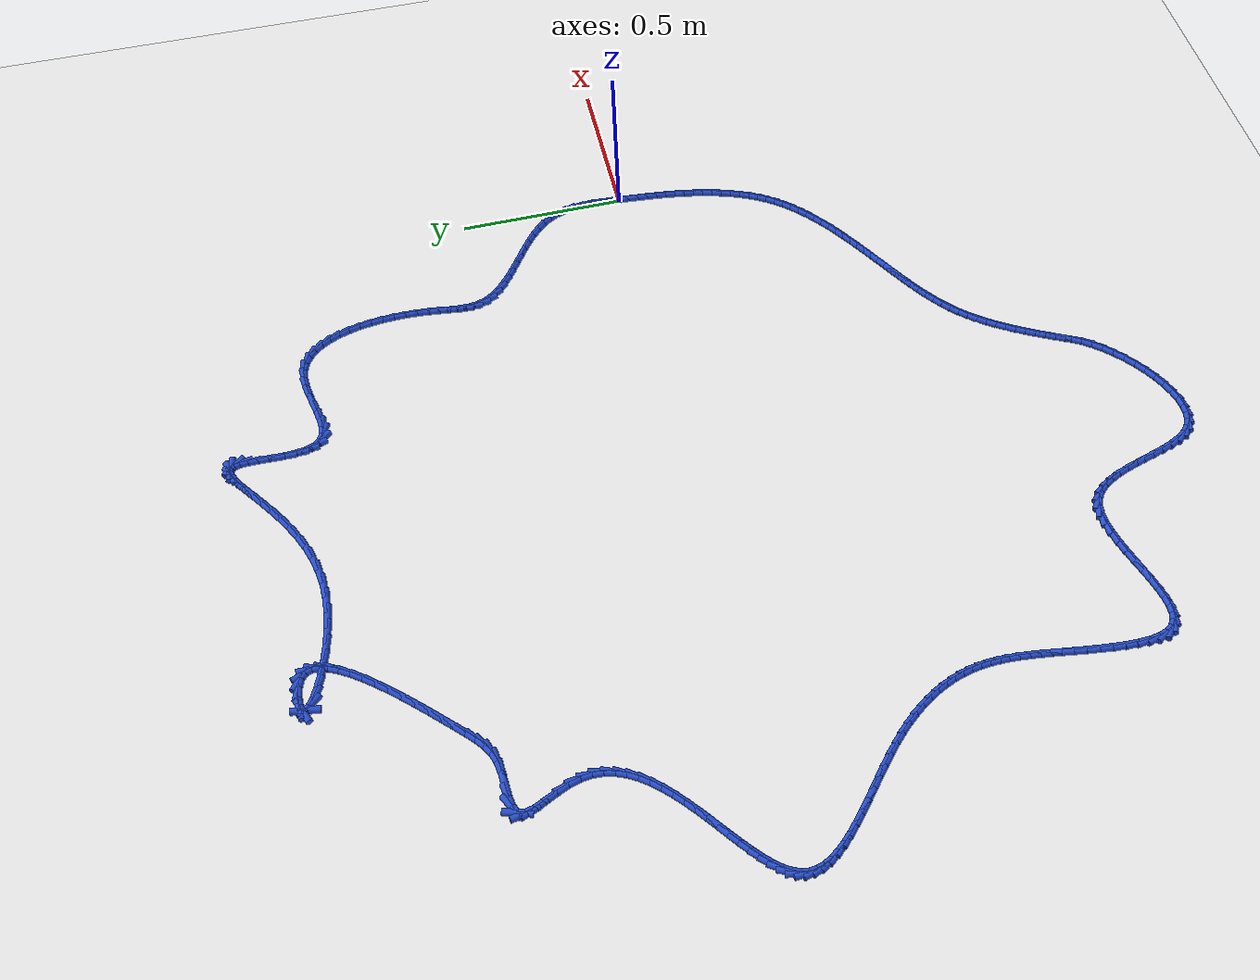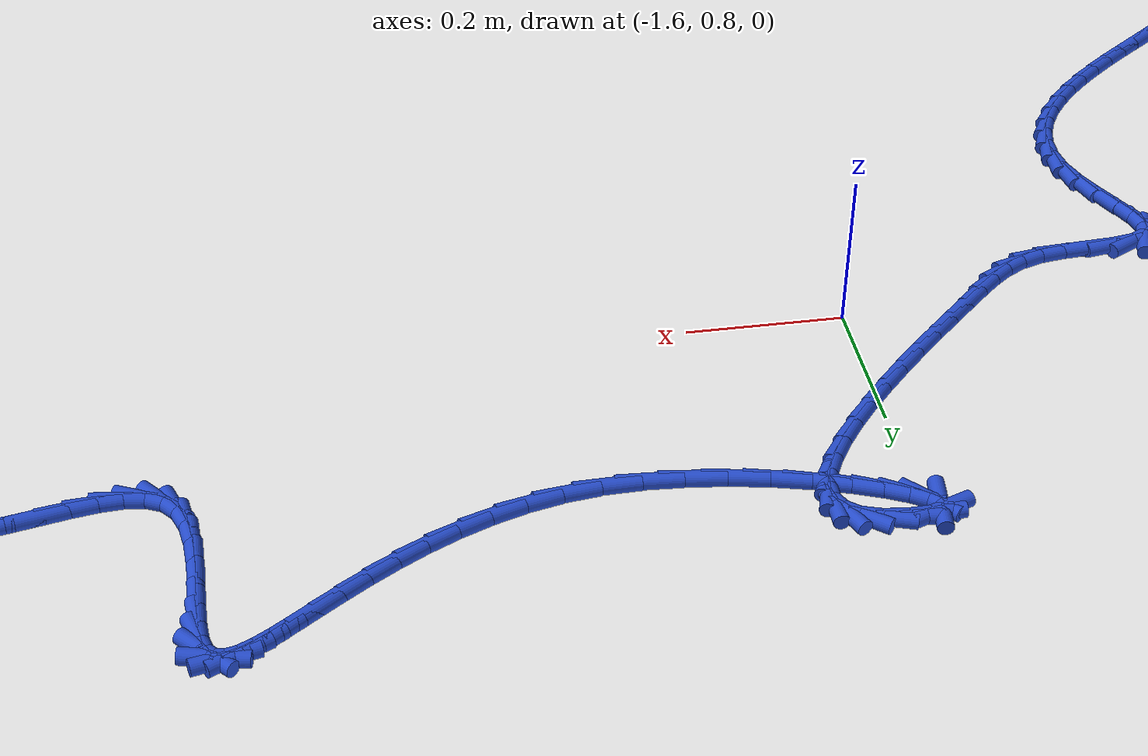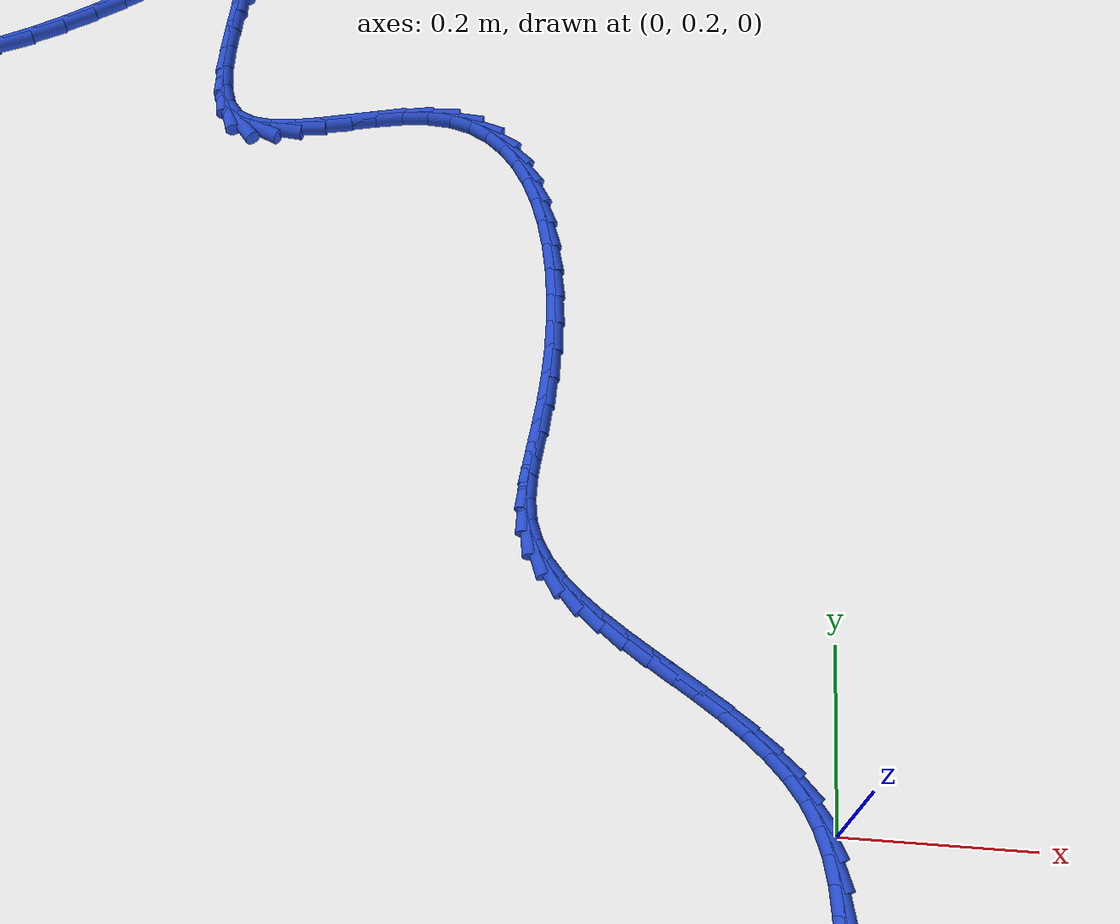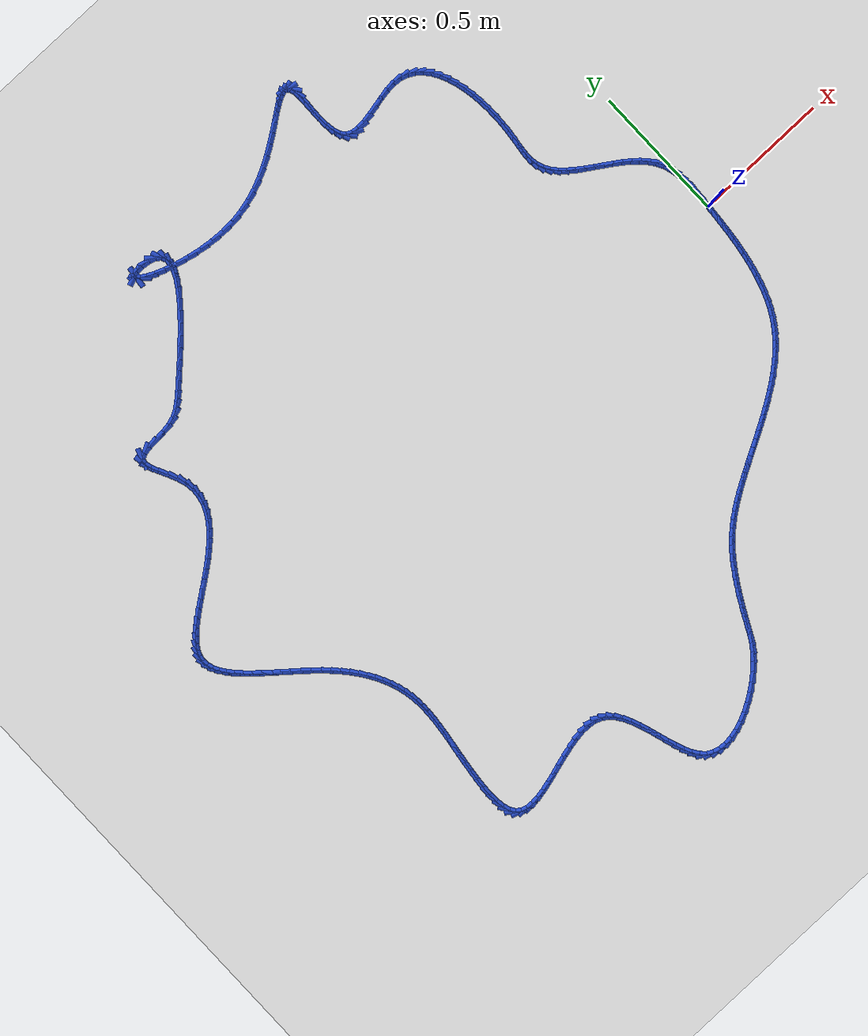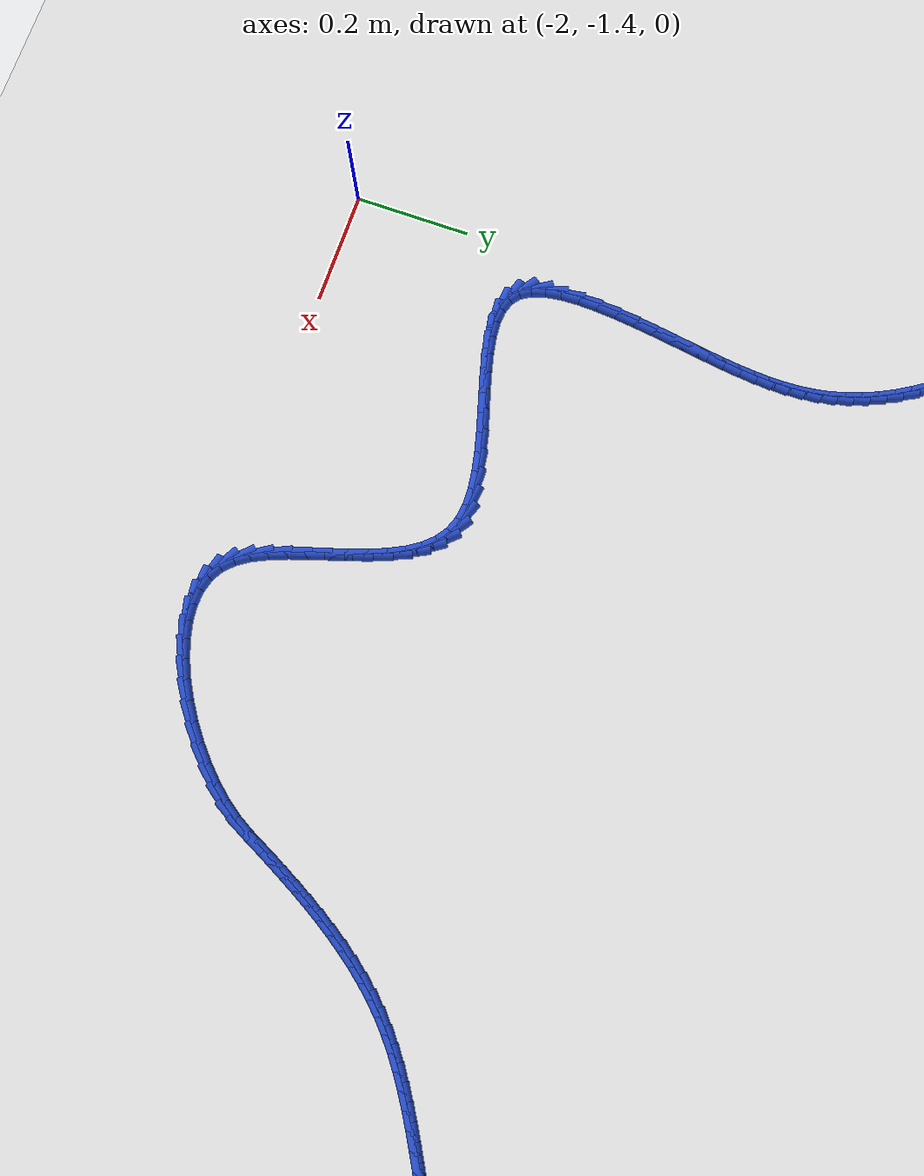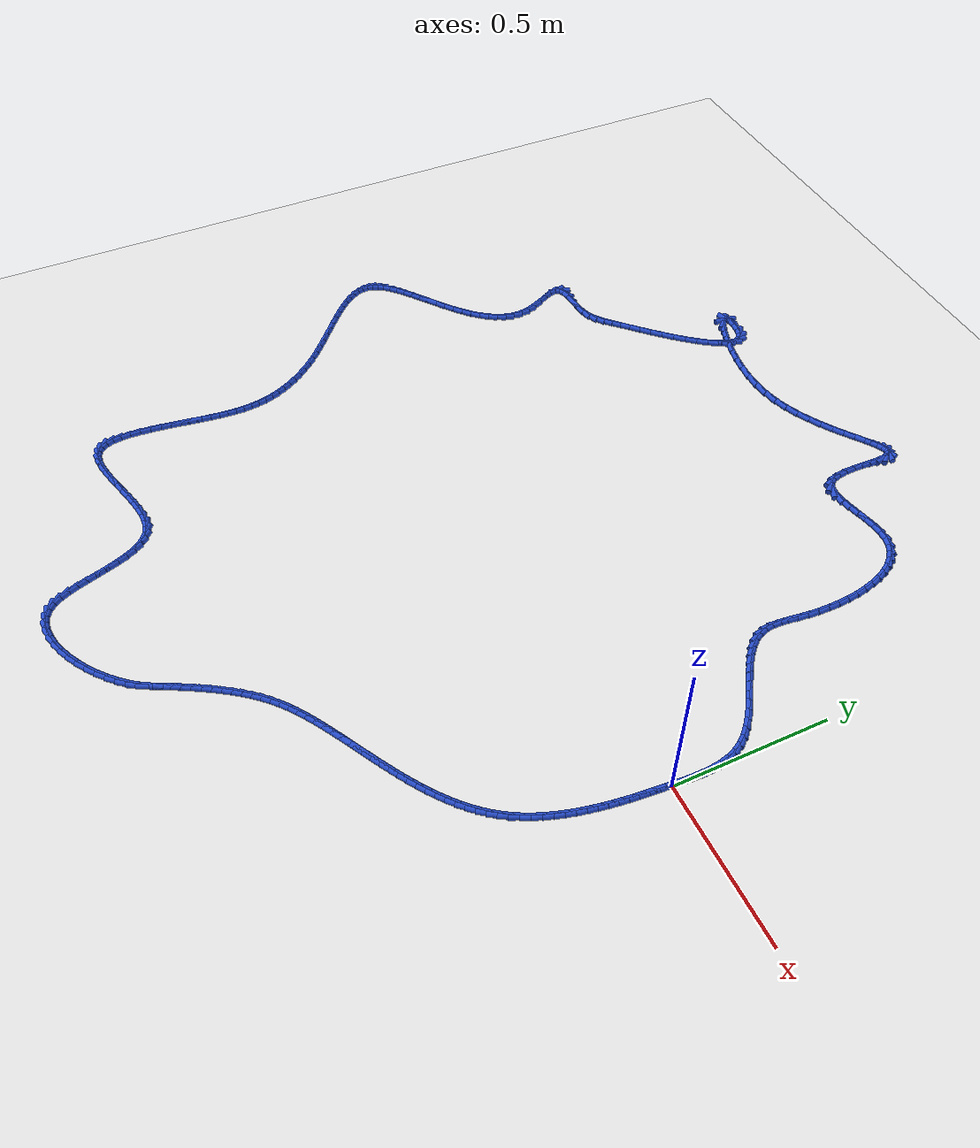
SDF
<sdf version="1.6">
 <world name="default">
  <light name="sun" type="directional">
   <pose>0 0 10 0 -0 0</pose>
   <diffuse>0.8 0.8 0.8 1</diffuse>
   <specular>0.2 0.2 0.2 1</specular>
   <attenuation>
    <range>1000</range>
    <constant>0.9</constant>
    <linear>0.01</linear>
    <quadratic>0.001</quadratic>
   </attenuation>
   <direction>-0.5 0.1 -0.9</direction>
  </light>
  <model name="ground_plane">
   <static>1</static>
   <link name="link">
    <collision name="collision">
     <geometry><plane><normal>0 0 1</normal><size>100 100</size></plane></geometry>
     <surface><friction><ode><mu>100</mu><mu2>50</mu2></ode></friction></surface>
    </collision>
    <visual name="visual">
     <cast_shadows>0</cast_shadows>
     <geometry><plane><normal>0 0 1</normal><size>100 100</size></plane></geometry>
     <material>
      <script><uri>file://media/materials/scripts/gazebo.material</uri><name>Gazebo/WhiteGlow</name></script>
     </material>
    </visual>
   </link>
  </model>
  <gravity>0 0 -9.8</gravity>
  <magnetic_field>6e-06 2.3e-05 -4.2e-05</magnetic_field>
  <atmosphere type="adiabatic"/>
  <physics name="default_physics" default="0" type="ode">
   <max_step_size>0.001</max_step_size>
   <real_time_factor>1</real_time_factor>
   <real_time_update_rate>1000</real_time_update_rate>
  </physics>
  <scene><ambient>0.4 0.4 0.4 1</ambient><background>0.7 0.7 0.7 1</background><shadows>1</shadows></scene>
  <spherical_coordinates>
   <surface_model>EARTH_WGS84</surface_model>
   <latitude_deg>0</latitude_deg>
   <longitude_deg>0</longitude_deg>
   <elevation>0</elevation>
   <heading_deg>0</heading_deg>
  </spherical_coordinates>
  <model name="line">
   <link name="link_0">
    <pose>-8.239936510889834e-18 -2.7755575615628914e-17 0.01 0 1.57 1.5055367131819806</pose>
    <collision name="collision">
     <geometry><cylinder><radius>0.01</radius><length>0.08</length></cylinder></geometry>
    </collision>
    <visual name="visual">
     <material>
      <script><name>Gazebo/Blue</name><uri>file://media/materials/scripts/gazebo.material</uri></script>
     </material>
     <geometry><cylinder><radius>0.01</radius><length>0.08</length></cylinder></geometry>
    </visual>
   </link>
   <link name="link_1">
    <pose>0.0020054013227905018 0.03068595604713026 0.01 0 1.57 1.5248557876471254</pose>
    <collision name="collision">
     <geometry><cylinder><radius>0.01</radius><length>0.08</length></cylinder></geometry>
    </collision>
    <visual name="visual">
     <material>
      <script><name>Gazebo/Blue</name><uri>file://media/materials/scripts/gazebo.material</uri></script>
     </material>
     <geometry><cylinder><radius>0.01</radius><length>0.08</length></cylinder></geometry>
    </visual>
   </link>
   <link name="link_2">
    <pose>0.0034254664954342694 0.06157514513458124 0.01 0 1.57 1.5615450401642117</pose>
    <collision name="collision">
     <geometry><cylinder><radius>0.01</radius><length>0.08</length></cylinder></geometry>
    </collision>
    <visual name="visual">
     <material>
      <script><name>Gazebo/Blue</name><uri>file://media/materials/scripts/gazebo.material</uri></script>
     </material>
     <geometry><cylinder><radius>0.01</radius><length>0.08</length></cylinder></geometry>
    </visual>
   </link>
   <link name="link_3">
    <pose>0.0037100426474062655 0.09233497829927455 0.01 0 1.57 -1.5245862306204465</pose>
    <collision name="collision">
     <geometry><cylinder><radius>0.01</radius><length>0.08</length></cylinder></geometry>
    </collision>
    <visual name="visual">
     <material>
      <script><name>Gazebo/Blue</name><uri>file://media/materials/scripts/gazebo.material</uri></script>
     </material>
     <geometry><cylinder><radius>0.01</radius><length>0.08</length></cylinder></geometry>
    </visual>
   </link>
   <link name="link_4">
    <pose>0.002308976908181463 0.12263286657813191 0.01 0 1.57 -1.4481456789380212</pose>
    <collision name="collision">
     <geometry><cylinder><radius>0.01</radius><length>0.08</length></cylinder></geometry>
    </collision>
    <visual name="visual">
     <material>
      <script><name>Gazebo/Blue</name><uri>file://media/materials/scripts/gazebo.material</uri></script>
     </material>
     <geometry><cylinder><radius>0.01</radius><length>0.08</length></cylinder></geometry>
    </visual>
   </link>
   <link name="link_5">
    <pose>-0.0013278835927651618 0.15213622100807495 0.01 0 1.57 -1.3482023990741532</pose>
    <collision name="collision">
     <geometry><cylinder><radius>0.01</radius><length>0.08</length></cylinder></geometry>
    </collision>
    <visual name="visual">
     <material>
      <script><name>Gazebo/Blue</name><uri>file://media/materials/scripts/gazebo.material</uri></script>
     </material>
     <geometry><cylinder><radius>0.01</radius><length>0.08</length></cylinder></geometry>
    </visual>
   </link>
   <link name="link_6">
    <pose>-0.0077506917259586375 0.1805124526260254 0.01 0 1.57 -1.222974496023746</pose>
    <collision name="collision">
     <geometry><cylinder><radius>0.01</radius><length>0.08</length></cylinder></geometry>
    </collision>
    <visual name="visual">
     <material>
      <script><name>Gazebo/Blue</name><uri>file://media/materials/scripts/gazebo.material</uri></script>
     </material>
     <geometry><cylinder><radius>0.01</radius><length>0.08</length></cylinder></geometry>
    </visual>
   </link>
   <link name="link_7">
    <pose>-0.017509600361923984 0.2074289724689049 0.01 0 1.57 -1.0737983760830216</pose>
    <collision name="collision">
     <geometry><cylinder><radius>0.01</radius><length>0.08</length></cylinder></geometry>
    </collision>
    <visual name="visual">
     <material>
      <script><name>Gazebo/Blue</name><uri>file://media/materials/scripts/gazebo.material</uri></script>
     </material>
     <geometry><cylinder><radius>0.01</radius><length>0.08</length></cylinder></geometry>
    </visual>
   </link>
   <link name="link_8">
    <pose>-0.031141001407778198 0.2325601083676116 0.01 0 1.57 -0.9252251454450983</pose>
    <collision name="collision">
     <geometry><cylinder><radius>0.01</radius><length>0.08</length></cylinder></geometry>
    </collision>
    <visual name="visual">
     <material>
      <script><name>Gazebo/Blue</name><uri>file://media/materials/scripts/gazebo.material</uri></script>
     </material>
     <geometry><cylinder><radius>0.01</radius><length>0.08</length></cylinder></geometry>
    </visual>
   </link>
   <link name="link_9">
    <pose>-0.048673055452506976 0.25583564492708116 0.01 0 1.57 -0.8055952407432211</pose>
    <collision name="collision">
     <geometry><cylinder><radius>0.01</radius><length>0.08</length></cylinder></geometry>
    </collision>
    <visual name="visual">
     <material>
      <script><name>Gazebo/Blue</name><uri>file://media/materials/scripts/gazebo.material</uri></script>
     </material>
     <geometry><cylinder><radius>0.01</radius><length>0.08</length></cylinder></geometry>
    </visual>
   </link>
   <link name="link_10">
    <pose>-0.06948877097055095 0.27750964522952143 0.01 0 1.57 -0.7148730877086096</pose>
    <collision name="collision">
     <geometry><cylinder><radius>0.01</radius><length>0.08</length></cylinder></geometry>
    </collision>
    <visual name="visual">
     <material>
      <script><name>Gazebo/Blue</name><uri>file://media/materials/scripts/gazebo.material</uri></script>
     </material>
     <geometry><cylinder><radius>0.01</radius><length>0.08</length></cylinder></geometry>
    </visual>
   </link>
   <link name="link_11">
    <pose>-0.0929295218885654 0.2978570994957995 0.01 0 1.57 -0.6495324747695036</pose>
    <collision name="collision">
     <geometry><cylinder><radius>0.01</radius><length>0.08</length></cylinder></geometry>
    </collision>
    <visual name="visual">
     <material>
      <script><name>Gazebo/Blue</name><uri>file://media/materials/scripts/gazebo.material</uri></script>
     </material>
     <geometry><cylinder><radius>0.01</radius><length>0.08</length></cylinder></geometry>
    </visual>
   </link>
   <link name="link_12">
    <pose>-0.11833668213320567 0.31715299794678276 0.01 0 1.57 -0.606161113369923</pose>
    <collision name="collision">
     <geometry><cylinder><radius>0.01</radius><length>0.08</length></cylinder></geometry>
    </collision>
    <visual name="visual">
     <material>
      <script><name>Gazebo/Blue</name><uri>file://media/materials/scripts/gazebo.material</uri></script>
     </material>
     <geometry><cylinder><radius>0.01</radius><length>0.08</length></cylinder></geometry>
    </visual>
   </link>
   <link name="link_13">
    <pose>-0.14505162563112706 0.3356723308033385 0.01 0 1.57 -0.5822891181065538</pose>
    <collision name="collision">
     <geometry><cylinder><radius>0.01</radius><length>0.08</length></cylinder></geometry>
    </collision>
    <visual name="visual">
     <material>
      <script><name>Gazebo/Blue</name><uri>file://media/materials/scripts/gazebo.material</uri></script>
     </material>
     <geometry><cylinder><radius>0.01</radius><length>0.08</length></cylinder></geometry>
    </visual>
   </link>
   <link name="link_14">
    <pose>-0.17241572630898475 0.3536900882863339 0.01 0 1.57 -0.5766491664591904</pose>
    <collision name="collision">
     <geometry><cylinder><radius>0.01</radius><length>0.08</length></cylinder></geometry>
    </collision>
    <visual name="visual">
     <material>
      <script><name>Gazebo/Blue</name><uri>file://media/materials/scripts/gazebo.material</uri></script>
     </material>
     <geometry><cylinder><radius>0.01</radius><length>0.08</length></cylinder></geometry>
    </visual>
   </link>
   <link name="link_15">
    <pose>-0.1997703580934342 0.37148126061663644 0.01 0 1.57 -0.5892611143224346</pose>
    <collision name="collision">
     <geometry><cylinder><radius>0.01</radius><length>0.08</length></cylinder></geometry>
    </collision>
    <visual name="visual">
     <material>
      <script><name>Gazebo/Blue</name><uri>file://media/materials/scripts/gazebo.material</uri></script>
     </material>
     <geometry><cylinder><radius>0.01</radius><length>0.08</length></cylinder></geometry>
    </visual>
   </link>
   <link name="link_16">
    <pose>-0.22645689491113064 0.3893208380151132 0.01 0 1.57 -0.6215230118221199</pose>
    <collision name="collision">
     <geometry><cylinder><radius>0.01</radius><length>0.08</length></cylinder></geometry>
    </collision>
    <visual name="visual">
     <material>
      <script><name>Gazebo/Blue</name><uri>file://media/materials/scripts/gazebo.material</uri></script>
     </material>
     <geometry><cylinder><radius>0.01</radius><length>0.08</length></cylinder></geometry>
    </visual>
   </link>
   <link name="link_17">
    <pose>-0.25181671068872935 0.4074838107026316 0.01 0 1.57 -0.6763505693773352</pose>
    <collision name="collision">
     <geometry><cylinder><radius>0.01</radius><length>0.08</length></cylinder></geometry>
    </collision>
    <visual name="visual">
     <material>
      <script><name>Gazebo/Blue</name><uri>file://media/materials/scripts/gazebo.material</uri></script>
     </material>
     <geometry><cylinder><radius>0.01</radius><length>0.08</length></cylinder></geometry>
    </visual>
   </link>
   <link name="link_18">
    <pose>-0.2751911793528856 0.4262451689000589 0.01 0 1.57 -0.7582586543871765</pose>
    <collision name="collision">
     <geometry><cylinder><radius>0.01</radius><length>0.08</length></cylinder></geometry>
    </collision>
    <visual name="visual">
     <material>
      <script><name>Gazebo/Blue</name><uri>file://media/materials/scripts/gazebo.material</uri></script>
     </material>
     <geometry><cylinder><radius>0.01</radius><length>0.08</length></cylinder></geometry>
    </visual>
   </link>
   <link name="link_19">
    <pose>-0.2959216748302549 0.4458799028282625 0.01 0 1.57 -0.8729808142229536</pose>
    <collision name="collision">
     <geometry><cylinder><radius>0.01</radius><length>0.08</length></cylinder></geometry>
    </collision>
    <visual name="visual">
     <material>
      <script><name>Gazebo/Blue</name><uri>file://media/materials/scripts/gazebo.material</uri></script>
     </material>
     <geometry><cylinder><radius>0.01</radius><length>0.08</length></cylinder></geometry>
    </visual>
   </link>
   <link name="link_20">
    <pose>-0.3133495710474923 0.46666300270810945 0.01 0 1.57 -1.0256619737185508</pose>
    <collision name="collision">
     <geometry><cylinder><radius>0.01</radius><length>0.08</length></cylinder></geometry>
    </collision>
    <visual name="visual">
     <material>
      <script><name>Gazebo/Blue</name><uri>file://media/materials/scripts/gazebo.material</uri></script>
     </material>
     <geometry><cylinder><radius>0.01</radius><length>0.08</length></cylinder></geometry>
    </visual>
   </link>
   <link name="link_21">
    <pose>-0.32681624193125325 0.4888694587604673 0.01 0 1.57 -1.2163412526721904</pose>
    <collision name="collision">
     <geometry><cylinder><radius>0.01</radius><length>0.08</length></cylinder></geometry>
    </collision>
    <visual name="visual">
     <material>
      <script><name>Gazebo/Blue</name><uri>file://media/materials/scripts/gazebo.material</uri></script>
     </material>
     <geometry><cylinder><radius>0.01</radius><length>0.08</length></cylinder></geometry>
    </visual>
   </link>
   <link name="link_22">
    <pose>-0.33566306140819296 0.5127742612062034 0.01 0 1.57 -1.421114778737632</pose>
    <collision name="collision">
     <geometry><cylinder><radius>0.01</radius><length>0.08</length></cylinder></geometry>
    </collision>
    <visual name="visual">
     <material>
      <script><name>Gazebo/Blue</name><uri>file://media/materials/scripts/gazebo.material</uri></script>
     </material>
     <geometry><cylinder><radius>0.01</radius><length>0.08</length></cylinder></geometry>
    </visual>
   </link>
   <link name="link_23">
    <pose>-0.3395571328438654 0.5385953880955044 0.01 0 1.57 1.5688354151365265</pose>
    <collision name="collision">
     <geometry><cylinder><radius>0.01</radius><length>0.08</length></cylinder></geometry>
    </collision>
    <visual name="visual">
     <material>
      <script><name>Gazebo/Blue</name><uri>file://media/materials/scripts/gazebo.material</uri></script>
     </material>
     <geometry><cylinder><radius>0.01</radius><length>0.08</length></cylinder></geometry>
    </visual>
   </link>
   <link name="link_24">
    <pose>-0.3395027736011683 0.5663167659512824 0.01 0 1.57 1.4811632080917554</pose>
    <collision name="collision">
     <geometry><cylinder><radius>0.01</radius><length>0.08</length></cylinder></geometry>
    </collision>
    <visual name="visual">
     <material>
      <script><name>Gazebo/Blue</name><uri>file://media/materials/scripts/gazebo.material</uri></script>
     </material>
     <geometry><cylinder><radius>0.01</radius><length>0.08</length></cylinder></geometry>
    </visual>
   </link>
   <link name="link_25">
    <pose>-0.3368474030931749 0.5958622684111115 0.01 0 1.57 1.4465270861183872</pose>
    <collision name="collision">
     <geometry><cylinder><radius>0.01</radius><length>0.08</length></cylinder></geometry>
    </collision>
    <visual name="visual">
     <material>
      <script><name>Gazebo/Blue</name><uri>file://media/materials/scripts/gazebo.material</uri></script>
     </material>
     <geometry><cylinder><radius>0.01</radius><length>0.08</length></cylinder></geometry>
    </visual>
   </link>
   <link name="link_26">
    <pose>-0.33293844095012587 0.6271557690745546 0.01 0 1.57 1.4555773377724874</pose>
    <collision name="collision">
     <geometry><cylinder><radius>0.01</radius><length>0.08</length></cylinder></geometry>
    </collision>
    <visual name="visual">
     <material>
      <script><name>Gazebo/Blue</name><uri>file://media/materials/scripts/gazebo.material</uri></script>
     </material>
     <geometry><cylinder><radius>0.01</radius><length>0.08</length></cylinder></geometry>
    </visual>
   </link>
   <link name="link_27">
    <pose>-0.32912330661153416 0.6601211414725179 0.01 0 1.57 1.495986587267553</pose>
    <collision name="collision">
     <geometry><cylinder><radius>0.01</radius><length>0.08</length></cylinder></geometry>
    </collision>
    <visual name="visual">
     <material>
      <script><name>Gazebo/Blue</name><uri>file://media/materials/scripts/gazebo.material</uri></script>
     </material>
     <geometry><cylinder><radius>0.01</radius><length>0.08</length></cylinder></geometry>
    </visual>
   </link>
   <link name="link_28">
    <pose>-0.32653865088241263 0.6946063872801921 0.01 0 1.57 1.541662106381964</pose>
    <collision name="collision">
     <geometry><cylinder><radius>0.01</radius><length>0.08</length></cylinder></geometry>
    </collision>
    <visual name="visual">
     <material>
      <script><name>Gazebo/Blue</name><uri>file://media/materials/scripts/gazebo.material</uri></script>
     </material>
     <geometry><cylinder><radius>0.01</radius><length>0.08</length></cylinder></geometry>
    </visual>
   </link>
   <link name="link_29">
    <pose>-0.3255023915303317 0.7301647831296748 0.01 0 1.57 -1.5533174904945293</pose>
    <collision name="collision">
     <geometry><cylinder><radius>0.01</radius><length>0.08</length></cylinder></geometry>
    </collision>
    <visual name="visual">
     <material>
      <script><name>Gazebo/Blue</name><uri>file://media/materials/scripts/gazebo.material</uri></script>
     </material>
     <geometry><cylinder><radius>0.01</radius><length>0.08</length></cylinder></geometry>
    </visual>
   </link>
   <link name="link_30">
    <pose>-0.32613367373583013 0.766278052098242 0.01 0 1.57 -1.5040084522253485</pose>
    <collision name="collision">
     <geometry><cylinder><radius>0.01</radius><length>0.08</length></cylinder></geometry>
    </collision>
    <visual name="visual">
     <material>
      <script><name>Gazebo/Blue</name><uri>file://media/materials/scripts/gazebo.material</uri></script>
     </material>
     <geometry><cylinder><radius>0.01</radius><length>0.08</length></cylinder></geometry>
    </visual>
   </link>
   <link name="link_31">
    <pose>-0.32855164267944714 0.8024279172631695 0.01 0 1.57 -1.45016203255996</pose>
    <collision name="collision">
     <geometry><cylinder><radius>0.01</radius><length>0.08</length></cylinder></geometry>
    </collision>
    <visual name="visual">
     <material>
      <script><name>Gazebo/Blue</name><uri>file://media/materials/scripts/gazebo.material</uri></script>
     </material>
     <geometry><cylinder><radius>0.01</radius><length>0.08</length></cylinder></geometry>
    </visual>
   </link>
   <link name="link_32">
    <pose>-0.33287544354172177 0.8380961017017343 0.01 0 1.57 -1.389673682978109</pose>
    <collision name="collision">
     <geometry><cylinder><radius>0.01</radius><length>0.08</length></cylinder></geometry>
    </collision>
    <visual name="visual">
     <material>
      <script><name>Gazebo/Blue</name><uri>file://media/materials/scripts/gazebo.material</uri></script>
     </material>
     <geometry><cylinder><radius>0.01</radius><length>0.08</length></cylinder></geometry>
    </visual>
   </link>
   <link name="link_33">
    <pose>-0.33922422150319304 0.8727643284912117 0.01 0 1.57 -1.3199945525088959</pose>
    <collision name="collision">
     <geometry><cylinder><radius>0.01</radius><length>0.08</length></cylinder></geometry>
    </collision>
    <visual name="visual">
     <material>
      <script><name>Gazebo/Blue</name><uri>file://media/materials/scripts/gazebo.material</uri></script>
     </material>
     <geometry><cylinder><radius>0.01</radius><length>0.08</length></cylinder></geometry>
    </visual>
   </link>
   <link name="link_34">
    <pose>-0.3477171217444001 0.9059143207088785 0.01 0 1.57 -1.2379505505037234</pose>
    <collision name="collision">
     <geometry><cylinder><radius>0.01</radius><length>0.08</length></cylinder></geometry>
    </collision>
    <visual name="visual">
     <material>
      <script><name>Gazebo/Blue</name><uri>file://media/materials/scripts/gazebo.material</uri></script>
     </material>
     <geometry><cylinder><radius>0.01</radius><length>0.08</length></cylinder></geometry>
    </visual>
   </link>
   <link name="link_35">
    <pose>-0.35847328944588197 0.9370278014320105 0.01 0 1.57 -1.1396118701778544</pose>
    <collision name="collision">
     <geometry><cylinder><radius>0.01</radius><length>0.08</length></cylinder></geometry>
    </collision>
    <visual name="visual">
     <material>
      <script><name>Gazebo/Blue</name><uri>file://media/materials/scripts/gazebo.material</uri></script>
     </material>
     <geometry><cylinder><radius>0.01</radius><length>0.08</length></cylinder></geometry>
    </visual>
   </link>
   <link name="link_36">
    <pose>-0.37161186978817784 0.9655864937378841 0.01 0 1.57 -1.0203752992261192</pose>
    <collision name="collision">
     <geometry><cylinder><radius>0.01</radius><length>0.08</length></cylinder></geometry>
    </collision>
    <visual name="visual">
     <material>
      <script><name>Gazebo/Blue</name><uri>file://media/materials/scripts/gazebo.material</uri></script>
     </material>
     <geometry><cylinder><radius>0.01</radius><length>0.08</length></cylinder></geometry>
    </visual>
   </link>
   <link name="link_37">
    <pose>-0.3872520079518267 0.9910721207037754 0.01 0 1.57 -0.8756375920364509</pose>
    <collision name="collision">
     <geometry><cylinder><radius>0.01</radius><length>0.08</length></cylinder></geometry>
    </collision>
    <visual name="visual">
     <material>
      <script><name>Gazebo/Blue</name><uri>file://media/materials/scripts/gazebo.material</uri></script>
     </material>
     <geometry><cylinder><radius>0.01</radius><length>0.08</length></cylinder></geometry>
    </visual>
   </link>
   <link name="link_38">
    <pose>-0.4055128491173675 1.0129664054069603 0.01 0 1.57 -0.7026689082415356</pose>
    <collision name="collision">
     <geometry><cylinder><radius>0.01</radius><length>0.08</length></cylinder></geometry>
    </collision>
    <visual name="visual">
     <material>
      <script><name>Gazebo/Blue</name><uri>file://media/materials/scripts/gazebo.material</uri></script>
     </material>
     <geometry><cylinder><radius>0.01</radius><length>0.08</length></cylinder></geometry>
    </visual>
   </link>
   <link name="link_39">
    <pose>-0.42651353846533946 1.0307510709247152 0.01 0 1.57 -0.5039347985222223</pose>
    <collision name="collision">
     <geometry><cylinder><radius>0.01</radius><length>0.08</length></cylinder></geometry>
    </collision>
    <visual name="visual">
     <material>
      <script><name>Gazebo/Blue</name><uri>file://media/materials/scripts/gazebo.material</uri></script>
     </material>
     <geometry><cylinder><radius>0.01</radius><length>0.08</length></cylinder></geometry>
    </visual>
   </link>
   <link name="link_40">
    <pose>-0.45037322117628154 1.0439078403343163 0.01 0 1.57 -0.2900632042792648</pose>
    <collision name="collision">
     <geometry><cylinder><radius>0.01</radius><length>0.08</length></cylinder></geometry>
    </collision>
    <visual name="visual">
     <material>
      <script><name>Gazebo/Blue</name><uri>file://media/materials/scripts/gazebo.material</uri></script>
     </material>
     <geometry><cylinder><radius>0.01</radius><length>0.08</length></cylinder></geometry>
    </visual>
   </link>
   <link name="link_41">
    <pose>-0.4772110424307331 1.05191843671304 0.01 0 1.57 -0.08105332584894963</pose>
    <collision name="collision">
     <geometry><cylinder><radius>0.01</radius><length>0.08</length></cylinder></geometry>
    </collision>
    <visual name="visual">
     <material>
      <script><name>Gazebo/Blue</name><uri>file://media/materials/scripts/gazebo.material</uri></script>
     </material>
     <geometry><cylinder><radius>0.01</radius><length>0.08</length></cylinder></geometry>
    </visual>
   </link>
   <link name="link_42">
    <pose>-0.5071016873078441 1.0543464923741948 0.01 0 1.57 0.07438077698261866</pose>
    <collision name="collision">
     <geometry><cylinder><radius>0.01</radius><length>0.08</length></cylinder></geometry>
    </collision>
    <visual name="visual">
     <material>
      <script><name>Gazebo/Blue</name><uri>file://media/materials/scripts/gazebo.material</uri></script>
     </material>
     <geometry><cylinder><radius>0.01</radius><length>0.08</length></cylinder></geometry>
    </visual>
   </link>
   <link name="link_43">
    <pose>-0.5394803999400526 1.0519336873142304 0.01 0 1.57 0.16491094727989716</pose>
    <collision name="collision">
     <geometry><cylinder><radius>0.01</radius><length>0.08</length></cylinder></geometry>
    </collision>
    <visual name="visual">
     <material>
      <script><name>Gazebo/Blue</name><uri>file://media/materials/scripts/gazebo.material</uri></script>
     </material>
     <geometry><cylinder><radius>0.01</radius><length>0.08</length></cylinder></geometry>
    </visual>
   </link>
   <link name="link_44">
    <pose>-0.573303058745685 1.0463048412030729 0.01 0 1.57 0.20739517713781389</pose>
    <collision name="collision">
     <geometry><cylinder><radius>0.01</radius><length>0.08</length></cylinder></geometry>
    </collision>
    <visual name="visual">
     <material>
      <script><name>Gazebo/Blue</name><uri>file://media/materials/scripts/gazebo.material</uri></script>
     </material>
     <geometry><cylinder><radius>0.01</radius><length>0.08</length></cylinder></geometry>
    </visual>
   </link>
   <link name="link_45">
    <pose>-0.6075139325860752 1.0391061620996551 0.01 0 1.57 0.20922395566981875</pose>
    <collision name="collision">
     <geometry><cylinder><radius>0.01</radius><length>0.08</length></cylinder></geometry>
    </collision>
    <visual name="visual">
     <material>
      <script><name>Gazebo/Blue</name><uri>file://media/materials/scripts/gazebo.material</uri></script>
     </material>
     <geometry><cylinder><radius>0.01</radius><length>0.08</length></cylinder></geometry>
    </visual>
   </link>
   <link name="link_46">
    <pose>-0.6410572903225589 1.031983858062911 0.01 0 1.57 0.16809393093126634</pose>
    <collision name="collision">
     <geometry><cylinder><radius>0.01</radius><length>0.08</length></cylinder></geometry>
    </collision>
    <visual name="visual">
     <material>
      <script><name>Gazebo/Blue</name><uri>file://media/materials/scripts/gazebo.material</uri></script>
     </material>
     <geometry><cylinder><radius>0.01</radius><length>0.08</length></cylinder></geometry>
    </visual>
   </link>
   <link name="link_47">
    <pose>-0.6728774008164701 1.0265841371517745 0.01 0 1.57 0.06981919899489512</pose>
    <collision name="collision">
     <geometry><cylinder><radius>0.01</radius><length>0.08</length></cylinder></geometry>
    </collision>
    <visual name="visual">
     <material>
      <script><name>Gazebo/Blue</name><uri>file://media/materials/scripts/gazebo.material</uri></script>
     </material>
     <geometry><cylinder><radius>0.01</radius><length>0.08</length></cylinder></geometry>
    </visual>
   </link>
   <link name="link_48">
    <pose>-0.7019185329291444 1.0245532074251793 0.01 0 1.57 -0.11783682985157118</pose>
    <collision name="collision">
     <geometry><cylinder><radius>0.01</radius><length>0.08</length></cylinder></geometry>
    </collision>
    <visual name="visual">
     <material>
      <script><name>Gazebo/Blue</name><uri>file://media/materials/scripts/gazebo.material</uri></script>
     </material>
     <geometry><cylinder><radius>0.01</radius><length>0.08</length></cylinder></geometry>
    </visual>
   </link>
   <link name="link_49">
    <pose>-0.7271249555219156 1.0275372769420579 0.01 0 1.57 -0.44325495950887006</pose>
    <collision name="collision">
     <geometry><cylinder><radius>0.01</radius><length>0.08</length></cylinder></geometry>
    </collision>
    <visual name="visual">
     <material>
      <script><name>Gazebo/Blue</name><uri>file://media/materials/scripts/gazebo.material</uri></script>
     </material>
     <geometry><cylinder><radius>0.01</radius><length>0.08</length></cylinder></geometry>
    </visual>
   </link>
   <link name="link_50">
    <pose>-0.7474409374561191 1.0371825537613448 0.01 0 1.57 -0.8888479600028352</pose>
    <collision name="collision">
     <geometry><cylinder><radius>0.01</radius><length>0.08</length></cylinder></geometry>
    </collision>
    <visual name="visual">
     <material>
      <script><name>Gazebo/Blue</name><uri>file://media/materials/scripts/gazebo.material</uri></script>
     </material>
     <geometry><cylinder><radius>0.01</radius><length>0.08</length></cylinder></geometry>
    </visual>
   </link>
   <link name="link_51">
    <pose>-0.7618979484859402 1.0549891901640607 0.01 0 1.57 -1.233575787511971</pose>
    <collision name="collision">
     <geometry><cylinder><radius>0.01</radius><length>0.08</length></cylinder></geometry>
    </collision>
    <visual name="visual">
     <material>
      <script><name>Gazebo/Blue</name><uri>file://media/materials/scripts/gazebo.material</uri></script>
     </material>
     <geometry><cylinder><radius>0.01</radius><length>0.08</length></cylinder></geometry>
    </visual>
   </link>
   <link name="link_52">
    <pose>-0.770788234737268 1.0803456206755673 0.01 0 1.57 -1.4232304259485271</pose>
    <collision name="collision">
     <geometry><cylinder><radius>0.01</radius><length>0.08</length></cylinder></geometry>
    </collision>
    <visual name="visual">
     <material>
      <script><name>Gazebo/Blue</name><uri>file://media/materials/scripts/gazebo.material</uri></script>
     </material>
     <geometry><cylinder><radius>0.01</radius><length>0.08</length></cylinder></geometry>
    </visual>
   </link>
   <link name="link_53">
    <pose>-0.7753525641820457 1.1110515679220343 0.01 0 1.57 -1.5264002954903875</pose>
    <collision name="collision">
     <geometry><cylinder><radius>0.01</radius><length>0.08</length></cylinder></geometry>
    </collision>
    <visual name="visual">
     <material>
      <script><name>Gazebo/Blue</name><uri>file://media/materials/scripts/gazebo.material</uri></script>
     </material>
     <geometry><cylinder><radius>0.01</radius><length>0.08</length></cylinder></geometry>
    </visual>
   </link>
   <link name="link_54">
    <pose>-0.77685486504506 1.1448679626246954 0.01 0 1.57 1.5622690475915566</pose>
    <collision name="collision">
     <geometry><cylinder><radius>0.01</radius><length>0.08</length></cylinder></geometry>
    </collision>
    <visual name="visual">
     <material>
      <script><name>Gazebo/Blue</name><uri>file://media/materials/scripts/gazebo.material</uri></script>
     </material>
     <geometry><cylinder><radius>0.01</radius><length>0.08</length></cylinder></geometry>
    </visual>
   </link>
   <link name="link_55">
    <pose>-0.7765590655510981 1.1795557355047872 0.01 0 1.57 1.5458924252806907</pose>
    <collision name="collision">
     <geometry><cylinder><radius>0.01</radius><length>0.08</length></cylinder></geometry>
    </collision>
    <visual name="visual">
     <material>
      <script><name>Gazebo/Blue</name><uri>file://media/materials/scripts/gazebo.material</uri></script>
     </material>
     <geometry><cylinder><radius>0.01</radius><length>0.08</length></cylinder></geometry>
    </visual>
   </link>
   <link name="link_56">
    <pose>-0.7757290939249464 1.212875817283543 0.01 0 1.57 1.5674235919796078</pose>
    <collision name="collision">
     <geometry><cylinder><radius>0.01</radius><length>0.08</length></cylinder></geometry>
    </collision>
    <visual name="visual">
     <material>
      <script><name>Gazebo/Blue</name><uri>file://media/materials/scripts/gazebo.material</uri></script>
     </material>
     <geometry><cylinder><radius>0.01</radius><length>0.08</length></cylinder></geometry>
    </visual>
   </link>
   <link name="link_57">
    <pose>-0.7756288783913917 1.2425891386821988 0.01 0 1.57 -1.4916295899030938</pose>
    <collision name="collision">
     <geometry><cylinder><radius>0.01</radius><length>0.08</length></cylinder></geometry>
    </collision>
    <visual name="visual">
     <material>
      <script><name>Gazebo/Blue</name><uri>file://media/materials/scripts/gazebo.material</uri></script>
     </material>
     <geometry><cylinder><radius>0.01</radius><length>0.08</length></cylinder></geometry>
    </visual>
   </link>
   <link name="link_58">
    <pose>-0.7775223471752208 1.2664566304219889 0.01 0 1.57 -1.2760250386366485</pose>
    <collision name="collision">
     <geometry><cylinder><radius>0.01</radius><length>0.08</length></cylinder></geometry>
    </collision>
    <visual name="visual">
     <material>
      <script><name>Gazebo/Blue</name><uri>file://media/materials/scripts/gazebo.material</uri></script>
     </material>
     <geometry><cylinder><radius>0.01</radius><length>0.08</length></cylinder></geometry>
    </visual>
   </link>
   <link name="link_59">
    <pose>-0.782460714802814 1.2827217844403203 0.01 0 1.57 -0.8311810726080536</pose>
    <collision name="collision">
     <geometry><cylinder><radius>0.01</radius><length>0.08</length></cylinder></geometry>
    </collision>
    <visual name="visual">
     <material>
      <script><name>Gazebo/Blue</name><uri>file://media/materials/scripts/gazebo.material</uri></script>
     </material>
     <geometry><cylinder><radius>0.01</radius><length>0.08</length></cylinder></geometry>
    </visual>
   </link>
   <link name="link_60">
    <pose>-0.7906048292974288 1.291647973602834 0.01 0 1.57 -0.20789837078167367</pose>
    <collision name="collision">
     <geometry><cylinder><radius>0.01</radius><length>0.08</length></cylinder></geometry>
    </collision>
    <visual name="visual">
     <material>
      <script><name>Gazebo/Blue</name><uri>file://media/materials/scripts/gazebo.material</uri></script>
     </material>
     <geometry><cylinder><radius>0.01</radius><length>0.08</length></cylinder></geometry>
    </visual>
   </link>
   <link name="link_61">
    <pose>-0.8018826147062852 1.294026980924564 0.01 0 1.57 0.23125044733251585</pose>
    <collision name="collision">
     <geometry><cylinder><radius>0.01</radius><length>0.08</length></cylinder></geometry>
    </collision>
    <visual name="visual">
     <material>
      <script><name>Gazebo/Blue</name><uri>file://media/materials/scripts/gazebo.material</uri></script>
     </material>
     <geometry><cylinder><radius>0.01</radius><length>0.08</length></cylinder></geometry>
    </visual>
   </link>
   <link name="link_62">
    <pose>-0.8162219943056115 1.2906505911696078 0.01 0 1.57 0.4485574477888663</pose>
    <collision name="collision">
     <geometry><cylinder><radius>0.01</radius><length>0.08</length></cylinder></geometry>
    </collision>
    <visual name="visual">
     <material>
      <script><name>Gazebo/Blue</name><uri>file://media/materials/scripts/gazebo.material</uri></script>
     </material>
     <geometry><cylinder><radius>0.01</radius><length>0.08</length></cylinder></geometry>
    </visual>
   </link>
   <link name="link_63">
    <pose>-0.8335508913716372 1.2823105891020627 0.01 0 1.57 0.5535352118681327</pose>
    <collision name="collision">
     <geometry><cylinder><radius>0.01</radius><length>0.08</length></cylinder></geometry>
    </collision>
    <visual name="visual">
     <material>
      <script><name>Gazebo/Blue</name><uri>file://media/materials/scripts/gazebo.material</uri></script>
     </material>
     <geometry><cylinder><radius>0.01</radius><length>0.08</length></cylinder></geometry>
    </visual>
   </link>
   <link name="link_64">
    <pose>-0.8537972291805915 1.2697987594860274 0.01 0 1.57 0.6027673184308271</pose>
    <collision name="collision">
     <geometry><cylinder><radius>0.01</radius><length>0.08</length></cylinder></geometry>
    </collision>
    <visual name="visual">
     <material>
      <script><name>Gazebo/Blue</name><uri>file://media/materials/scripts/gazebo.material</uri></script>
     </material>
     <geometry><cylinder><radius>0.01</radius><length>0.08</length></cylinder></geometry>
    </visual>
   </link>
   <link name="link_65">
    <pose>-0.8768889310087031 1.253906887085599 0.01 0 1.57 0.6203810149422853</pose>
    <collision name="collision">
     <geometry><cylinder><radius>0.01</radius><length>0.08</length></cylinder></geometry>
    </collision>
    <visual name="visual">
     <material>
      <script><name>Gazebo/Blue</name><uri>file://media/materials/scripts/gazebo.material</uri></script>
     </material>
     <geometry><cylinder><radius>0.01</radius><length>0.08</length></cylinder></geometry>
    </visual>
   </link>
   <link name="link_66">
    <pose>-0.9027539201322017 1.2354267566648751 0.01 0 1.57 0.6172802450716407</pose>
    <collision name="collision">
     <geometry><cylinder><radius>0.01</radius><length>0.08</length></cylinder></geometry>
    </collision>
    <visual name="visual">
     <material>
      <script><name>Gazebo/Blue</name><uri>file://media/materials/scripts/gazebo.material</uri></script>
     </material>
     <geometry><cylinder><radius>0.01</radius><length>0.08</length></cylinder></geometry>
    </visual>
   </link>
   <link name="link_67">
    <pose>-0.931320119827316 1.2151501529879543 0.01 0 1.57 0.5986759002125898</pose>
    <collision name="collision">
     <geometry><cylinder><radius>0.01</radius><length>0.08</length></cylinder></geometry>
    </collision>
    <visual name="visual">
     <material>
      <script><name>Gazebo/Blue</name><uri>file://media/materials/scripts/gazebo.material</uri></script>
     </material>
     <geometry><cylinder><radius>0.01</radius><length>0.08</length></cylinder></geometry>
    </visual>
   </link>
   <link name="link_68">
    <pose>-0.9625154533702756 1.1938688608189338 0.01 0 1.57 0.5670539417128708</pose>
    <collision name="collision">
     <geometry><cylinder><radius>0.01</radius><length>0.08</length></cylinder></geometry>
    </collision>
    <visual name="visual">
     <material>
      <script><name>Gazebo/Blue</name><uri>file://media/materials/scripts/gazebo.material</uri></script>
     </material>
     <geometry><cylinder><radius>0.01</radius><length>0.08</length></cylinder></geometry>
    </visual>
   </link>
   <link name="link_69">
    <pose>-0.996267844037309 1.1723746649219118 0.01 0 1.57 0.5234675251830496</pose>
    <collision name="collision">
     <geometry><cylinder><radius>0.01</radius><length>0.08</length></cylinder></geometry>
    </collision>
    <visual name="visual">
     <material>
      <script><name>Gazebo/Blue</name><uri>file://media/materials/scripts/gazebo.material</uri></script>
     </material>
     <geometry><cylinder><radius>0.01</radius><length>0.08</length></cylinder></geometry>
    </visual>
   </link>
   <link name="link_70">
    <pose>-1.032505215104646 1.151459350060986 0.01 0 1.57 0.4681808267219978</pose>
    <collision name="collision">
     <geometry><cylinder><radius>0.01</radius><length>0.08</length></cylinder></geometry>
    </collision>
    <visual name="visual">
     <material>
      <script><name>Gazebo/Blue</name><uri>file://media/materials/scripts/gazebo.material</uri></script>
     </material>
     <geometry><cylinder><radius>0.01</radius><length>0.08</length></cylinder></geometry>
    </visual>
   </link>
   <link name="link_71">
    <pose>-1.071155489848515 1.1319147010002537 0.01 0 1.57 0.40106409727698217</pose>
    <collision name="collision">
     <geometry><cylinder><radius>0.01</radius><length>0.08</length></cylinder></geometry>
    </collision>
    <visual name="visual">
     <material>
      <script><name>Gazebo/Blue</name><uri>file://media/materials/scripts/gazebo.material</uri></script>
     </material>
     <geometry><cylinder><radius>0.01</radius><length>0.08</length></cylinder></geometry>
    </visual>
   </link>
   <link name="link_72">
    <pose>-1.1121465915451452 1.1145325025038129 0.01 0 1.57 0.32191724180992304</pose>
    <collision name="collision">
     <geometry><cylinder><radius>0.01</radius><length>0.08</length></cylinder></geometry>
    </collision>
    <visual name="visual">
     <material>
      <script><name>Gazebo/Blue</name><uri>file://media/materials/scripts/gazebo.material</uri></script>
     </material>
     <geometry><cylinder><radius>0.01</radius><length>0.08</length></cylinder></geometry>
    </visual>
   </link>
   <link name="link_73">
    <pose>-1.1554064434707672 1.1001045393357618 0.01 0 1.57 0.23080486381062618</pose>
    <collision name="collision">
     <geometry><cylinder><radius>0.01</radius><length>0.08</length></cylinder></geometry>
    </collision>
    <visual name="visual">
     <material>
      <script><name>Gazebo/Blue</name><uri>file://media/materials/scripts/gazebo.material</uri></script>
     </material>
     <geometry><cylinder><radius>0.01</radius><length>0.08</length></cylinder></geometry>
    </visual>
   </link>
   <link name="link_74">
    <pose>-1.200862968901608 1.089422596260198 0.01 0 1.57 0.12851327828109582</pose>
    <collision name="collision">
     <geometry><cylinder><radius>0.01</radius><length>0.08</length></cylinder></geometry>
    </collision>
    <visual name="visual">
     <material>
      <script><name>Gazebo/Blue</name><uri>file://media/materials/scripts/gazebo.material</uri></script>
     </material>
     <geometry><cylinder><radius>0.01</radius><length>0.08</length></cylinder></geometry>
    </visual>
   </link>
   <link name="link_75">
    <pose>-1.2484409251482966 1.083274312140309 0.01 0 1.57 0.026599533000685127</pose>
    <collision name="collision">
     <geometry><cylinder><radius>0.01</radius><length>0.08</length></cylinder></geometry>
    </collision>
    <visual name="visual">
     <material>
      <script><name>Gazebo/Blue</name><uri>file://media/materials/scripts/gazebo.material</uri></script>
     </material>
     <geometry><cylinder><radius>0.01</radius><length>0.08</length></cylinder></geometry>
    </visual>
   </link>
   <link name="link_76">
    <pose>-1.297695865137241 1.0819638446567752 0.01 0 1.57 -0.058235870590921515</pose>
    <collision name="collision">
     <geometry><cylinder><radius>0.01</radius><length>0.08</length></cylinder></geometry>
    </collision>
    <visual name="visual">
     <material>
      <script><name>Gazebo/Blue</name><uri>file://media/materials/scripts/gazebo.material</uri></script>
     </material>
     <geometry><cylinder><radius>0.01</radius><length>0.08</length></cylinder></geometry>
    </visual>
   </link>
   <link name="link_77">
    <pose>-1.3474736373649066 1.0848659780817163 0.01 0 1.57 -0.12938521683202794</pose>
    <collision name="collision">
     <geometry><cylinder><radius>0.01</radius><length>0.08</length></cylinder></geometry>
    </collision>
    <visual name="visual">
     <material>
      <script><name>Gazebo/Blue</name><uri>file://media/materials/scripts/gazebo.material</uri></script>
     </material>
     <geometry><cylinder><radius>0.01</radius><length>0.08</length></cylinder></geometry>
    </visual>
   </link>
   <link name="link_78">
    <pose>-1.396539565694319 1.0912500479259115 0.01 0 1.57 -0.1915006198650786</pose>
    <collision name="collision">
     <geometry><cylinder><radius>0.01</radius><length>0.08</length></cylinder></geometry>
    </collision>
    <visual name="visual">
     <material>
      <script><name>Gazebo/Blue</name><uri>file://media/materials/scripts/gazebo.material</uri></script>
     </material>
     <geometry><cylinder><radius>0.01</radius><length>0.08</length></cylinder></geometry>
    </visual>
   </link>
   <link name="link_79">
    <pose>-1.4436589739885026 1.1003853897001428 0.01 0 1.57 -0.24864666416244832</pose>
    <collision name="collision">
     <geometry><cylinder><radius>0.01</radius><length>0.08</length></cylinder></geometry>
    </collision>
    <visual name="visual">
     <material>
      <script><name>Gazebo/Blue</name><uri>file://media/materials/scripts/gazebo.material</uri></script>
     </material>
     <geometry><cylinder><radius>0.01</radius><length>0.08</length></cylinder></geometry>
    </visual>
   </link>
   <link name="link_80">
    <pose>-1.4875971861104844 1.1115413389151905 0.01 0 1.57 -0.3050769240678206</pose>
    <collision name="collision">
     <geometry><cylinder><radius>0.01</radius><length>0.08</length></cylinder></geometry>
    </collision>
    <visual name="visual">
     <material>
      <script><name>Gazebo/Blue</name><uri>file://media/materials/scripts/gazebo.material</uri></script>
     </material>
     <geometry><cylinder><radius>0.01</radius><length>0.08</length></cylinder></geometry>
    </visual>
   </link>
   <link name="link_81">
    <pose>-1.5271195259232888 1.1239872310818355 0.01 0 1.57 -0.36659654412472364</pose>
    <collision name="collision">
     <geometry><cylinder><radius>0.01</radius><length>0.08</length></cylinder></geometry>
    </collision>
    <visual name="visual">
     <material>
      <script><name>Gazebo/Blue</name><uri>file://media/materials/scripts/gazebo.material</uri></script>
     </material>
     <geometry><cylinder><radius>0.01</radius><length>0.08</length></cylinder></geometry>
    </visual>
   </link>
   <link name="link_82">
    <pose>-1.5609913172899423 1.1369924017108584 0.01 0 1.57 -0.44390674574400135</pose>
    <collision name="collision">
     <geometry><cylinder><radius>0.01</radius><length>0.08</length></cylinder></geometry>
    </collision>
    <visual name="visual">
     <material>
      <script><name>Gazebo/Blue</name><uri>file://media/materials/scripts/gazebo.material</uri></script>
     </material>
     <geometry><cylinder><radius>0.01</radius><length>0.08</length></cylinder></geometry>
    </visual>
   </link>
   <link name="link_83">
    <pose>-1.5879778840734695 1.14982618631304 0.01 0 1.57 -0.5639201812960966</pose>
    <collision name="collision">
     <geometry><cylinder><radius>0.01</radius><length>0.08</length></cylinder></geometry>
    </collision>
    <visual name="visual">
     <material>
      <script><name>Gazebo/Blue</name><uri>file://media/materials/scripts/gazebo.material</uri></script>
     </material>
     <geometry><cylinder><radius>0.01</radius><length>0.08</length></cylinder></geometry>
    </visual>
   </link>
   <link name="link_84">
    <pose>-1.606844550136896 1.1617579203991606 0.01 0 1.57 -0.8250989403229553</pose>
    <collision name="collision">
     <geometry><cylinder><radius>0.01</radius><length>0.08</length></cylinder></geometry>
    </collision>
    <visual name="visual">
     <material>
      <script><name>Gazebo/Blue</name><uri>file://media/materials/scripts/gazebo.material</uri></script>
     </material>
     <geometry><cylinder><radius>0.01</radius><length>0.08</length></cylinder></geometry>
    </visual>
   </link>
   <link name="link_85">
    <pose>-1.6163566393432467 1.1720569394800011 0.01 0 1.57 1.4358833813622178</pose>
    <collision name="collision">
     <geometry><cylinder><radius>0.01</radius><length>0.08</length></cylinder></geometry>
    </collision>
    <visual name="visual">
     <material>
      <script><name>Gazebo/Blue</name><uri>file://media/materials/scripts/gazebo.material</uri></script>
     </material>
     <geometry><cylinder><radius>0.01</radius><length>0.08</length></cylinder></geometry>
    </visual>
   </link>
   <link name="link_86">
    <pose>-1.615279475555548 1.1799925790663428 0.01 0 1.57 0.35902111773574996</pose>
    <collision name="collision">
     <geometry><cylinder><radius>0.01</radius><length>0.08</length></cylinder></geometry>
    </collision>
    <visual name="visual">
     <material>
      <script><name>Gazebo/Blue</name><uri>file://media/materials/scripts/gazebo.material</uri></script>
     </material>
     <geometry><cylinder><radius>0.01</radius><length>0.08</length></cylinder></geometry>
    </visual>
   </link>
   <link name="link_87">
    <pose>-1.6023783826368245 1.1848341746689655 0.01 0 1.57 0.04044553245227967</pose>
    <collision name="collision">
     <geometry><cylinder><radius>0.01</radius><length>0.08</length></cylinder></geometry>
    </collision>
    <visual name="visual">
     <material>
      <script><name>Gazebo/Blue</name><uri>file://media/materials/scripts/gazebo.material</uri></script>
     </material>
     <geometry><cylinder><radius>0.01</radius><length>0.08</length></cylinder></geometry>
    </visual>
   </link>
   <link name="link_88">
    <pose>-1.5770045467909755 1.185860992935017 0.01 0 1.57 -0.10934180423126734</pose>
    <collision name="collision">
     <geometry><cylinder><radius>0.01</radius><length>0.08</length></cylinder></geometry>
    </collision>
    <visual name="visual">
     <material>
      <script><name>Gazebo/Blue</name><uri>file://media/materials/scripts/gazebo.material</uri></script>
     </material>
     <geometry><cylinder><radius>0.01</radius><length>0.08</length></cylinder></geometry>
    </visual>
   </link>
   <link name="link_89">
    <pose>-1.5462365171797285 1.1824832894657678 0.01 0 1.57 -0.3199962306887712</pose>
    <collision name="collision">
     <geometry><cylinder><radius>0.01</radius><length>0.08</length></cylinder></geometry>
    </collision>
    <visual name="visual">
     <material>
      <script><name>Gazebo/Blue</name><uri>file://media/materials/scripts/gazebo.material</uri></script>
     </material>
     <geometry><cylinder><radius>0.01</radius><length>0.08</length></cylinder></geometry>
    </visual>
   </link>
   <link name="link_90">
    <pose>-1.5215011064763073 1.1742863398991352 0.01 0 1.57 -0.6865697448410042</pose>
    <collision name="collision">
     <geometry><cylinder><radius>0.01</radius><length>0.08</length></cylinder></geometry>
    </collision>
    <visual name="visual">
     <material>
      <script><name>Gazebo/Blue</name><uri>file://media/materials/scripts/gazebo.material</uri></script>
     </material>
     <geometry><cylinder><radius>0.01</radius><length>0.08</length></cylinder></geometry>
    </visual>
   </link>
   <link name="link_91">
    <pose>-1.5058828750123177 1.1614858640419299 0.01 0 1.57 -1.1626157298871223</pose>
    <collision name="collision">
     <geometry><cylinder><radius>0.01</radius><length>0.08</length></cylinder></geometry>
    </collision>
    <visual name="visual">
     <material>
      <script><name>Gazebo/Blue</name><uri>file://media/materials/scripts/gazebo.material</uri></script>
     </material>
     <geometry><cylinder><radius>0.01</radius><length>0.08</length></cylinder></geometry>
    </visual>
   </link>
   <link name="link_92">
    <pose>-1.4985745441587248 1.14458680982827 0.01 0 1.57 1.5623219765023986</pose>
    <collision name="collision">
     <geometry><cylinder><radius>0.01</radius><length>0.08</length></cylinder></geometry>
    </collision>
    <visual name="visual">
     <material>
      <script><name>Gazebo/Blue</name><uri>file://media/materials/scripts/gazebo.material</uri></script>
     </material>
     <geometry><cylinder><radius>0.01</radius><length>0.08</length></cylinder></geometry>
    </visual>
   </link>
   <link name="link_93">
    <pose>-1.498748197506376 1.1240956589213293 0.01 0 1.57 1.2889122293166329</pose>
    <collision name="collision">
     <geometry><cylinder><radius>0.01</radius><length>0.08</length></cylinder></geometry>
    </collision>
    <visual name="visual">
     <material>
      <script><name>Gazebo/Blue</name><uri>file://media/materials/scripts/gazebo.material</uri></script>
     </material>
     <geometry><cylinder><radius>0.01</radius><length>0.08</length></cylinder></geometry>
    </visual>
   </link>
   <link name="link_94">
    <pose>-1.5055759186461204 1.1005188929842822 0.01 0 1.57 1.1202033982301423</pose>
    <collision name="collision">
     <geometry><cylinder><radius>0.01</radius><length>0.08</length></cylinder></geometry>
    </collision>
    <visual name="visual">
     <material>
      <script><name>Gazebo/Blue</name><uri>file://media/materials/scripts/gazebo.material</uri></script>
     </material>
     <geometry><cylinder><radius>0.01</radius><length>0.08</length></cylinder></geometry>
    </visual>
   </link>
   <link name="link_95">
    <pose>-1.5182297911688052 1.0743629936803012 0.01 0 1.57 1.0119610753167925</pose>
    <collision name="collision">
     <geometry><cylinder><radius>0.01</radius><length>0.08</length></cylinder></geometry>
    </collision>
    <visual name="visual">
     <material>
      <script><name>Gazebo/Blue</name><uri>file://media/materials/scripts/gazebo.material</uri></script>
     </material>
     <geometry><cylinder><radius>0.01</radius><length>0.08</length></cylinder></geometry>
    </visual>
   </link>
   <link name="link_96">
    <pose>-1.5358818986652787 1.0461344426725614 0.01 0 1.57 0.9386378262210514</pose>
    <collision name="collision">
     <geometry><cylinder><radius>0.01</radius><length>0.08</length></cylinder></geometry>
    </collision>
    <visual name="visual">
     <material>
      <script><name>Gazebo/Blue</name><uri>file://media/materials/scripts/gazebo.material</uri></script>
     </material>
     <geometry><cylinder><radius>0.01</radius><length>0.08</length></cylinder></geometry>
    </visual>
   </link>
   <link name="link_97">
    <pose>-1.5577043247263889 1.0163397216242362 0.01 0 1.57 0.8866158558184885</pose>
    <collision name="collision">
     <geometry><cylinder><radius>0.01</radius><length>0.08</length></cylinder></geometry>
    </collision>
    <visual name="visual">
     <material>
      <script><name>Gazebo/Blue</name><uri>file://media/materials/scripts/gazebo.material</uri></script>
     </material>
     <geometry><cylinder><radius>0.01</radius><length>0.08</length></cylinder></geometry>
    </visual>
   </link>
   <link name="link_98">
    <pose>-1.5828691529429832 0.9854853121984997 0.01 0 1.57 0.8484132153327021</pose>
    <collision name="collision">
     <geometry><cylinder><radius>0.01</radius><length>0.08</length></cylinder></geometry>
    </collision>
    <visual name="visual">
     <material>
      <script><name>Gazebo/Blue</name><uri>file://media/materials/scripts/gazebo.material</uri></script>
     </material>
     <geometry><cylinder><radius>0.01</radius><length>0.08</length></cylinder></geometry>
    </visual>
   </link>
   <link name="link_99">
    <pose>-1.6105484669059107 0.9540776960585254 0.01 0 1.57 0.8197228908387896</pose>
    <collision name="collision">
     <geometry><cylinder><radius>0.01</radius><length>0.08</length></cylinder></geometry>
    </collision>
    <visual name="visual">
     <material>
      <script><name>Gazebo/Blue</name><uri>file://media/materials/scripts/gazebo.material</uri></script>
     </material>
     <geometry><cylinder><radius>0.01</radius><length>0.08</length></cylinder></geometry>
    </visual>
   </link>
   <link name="link_100">
    <pose>-1.6399143502060196 0.9226233548674873 0.01 0 1.57 0.7979760595204933</pose>
    <collision name="collision">
     <geometry><cylinder><radius>0.01</radius><length>0.08</length></cylinder></geometry>
    </collision>
    <visual name="visual">
     <material>
      <script><name>Gazebo/Blue</name><uri>file://media/materials/scripts/gazebo.material</uri></script>
     </material>
     <geometry><cylinder><radius>0.01</radius><length>0.08</length></cylinder></geometry>
    </visual>
   </link>
   <link name="link_101">
    <pose>-1.6701388864341564 0.8916287702885595 0.01 0 1.57 0.7816338676385163</pose>
    <collision name="collision">
     <geometry><cylinder><radius>0.01</radius><length>0.08</length></cylinder></geometry>
    </collision>
    <visual name="visual">
     <material>
      <script><name>Gazebo/Blue</name><uri>file://media/materials/scripts/gazebo.material</uri></script>
     </material>
     <geometry><cylinder><radius>0.01</radius><length>0.08</length></cylinder></geometry>
    </visual>
   </link>
   <link name="link_102">
    <pose>-1.7003941591811702 0.8616004239849155 0.01 0 1.57 0.7698433305456723</pose>
    <collision name="collision">
     <geometry><cylinder><radius>0.01</radius><length>0.08</length></cylinder></geometry>
    </collision>
    <visual name="visual">
     <material>
      <script><name>Gazebo/Blue</name><uri>file://media/materials/scripts/gazebo.material</uri></script>
     </material>
     <geometry><cylinder><radius>0.01</radius><length>0.08</length></cylinder></geometry>
    </visual>
   </link>
   <link name="link_103">
    <pose>-1.7298522520379094 0.8330447976197297 0.01 0 1.57 0.7623075215573222</pose>
    <collision name="collision">
     <geometry><cylinder><radius>0.01</radius><length>0.08</length></cylinder></geometry>
    </collision>
    <visual name="visual">
     <material>
      <script><name>Gazebo/Blue</name><uri>file://media/materials/scripts/gazebo.material</uri></script>
     </material>
     <geometry><cylinder><radius>0.01</radius><length>0.08</length></cylinder></geometry>
    </visual>
   </link>
   <link name="link_104">
    <pose>-1.7576852485952212 0.806468372856175 0.01 0 1.57 0.7589158713138348</pose>
    <collision name="collision">
     <geometry><cylinder><radius>0.01</radius><length>0.08</length></cylinder></geometry>
    </collision>
    <visual name="visual">
     <material>
      <script><name>Gazebo/Blue</name><uri>file://media/materials/scripts/gazebo.material</uri></script>
     </material>
     <geometry><cylinder><radius>0.01</radius><length>0.08</length></cylinder></geometry>
    </visual>
   </link>
   <link name="link_105">
    <pose>-1.7830872639056339 0.7823773530445015 0.01 0 1.57 0.7372895274767448</pose>
    <collision name="collision">
     <geometry><cylinder><radius>0.01</radius><length>0.08</length></cylinder></geometry>
    </collision>
    <visual name="visual">
     <material>
      <script><name>Gazebo/Blue</name><uri>file://media/materials/scripts/gazebo.material</uri></script>
     </material>
     <geometry><cylinder><radius>0.01</radius><length>0.08</length></cylinder></geometry>
    </visual>
   </link>
   <link name="link_106">
    <pose>-1.8063362123127233 0.7612642504165584 0.01 0 1.57 0.6563607282078129</pose>
    <collision name="collision">
     <geometry><cylinder><radius>0.01</radius><length>0.08</length></cylinder></geometry>
    </collision>
    <visual name="visual">
     <material>
      <script><name>Gazebo/Blue</name><uri>file://media/materials/scripts/gazebo.material</uri></script>
     </material>
     <geometry><cylinder><radius>0.01</radius><length>0.08</length></cylinder></geometry>
    </visual>
   </link>
   <link name="link_107">
    <pose>-1.8292656620702075 0.7436019253719346 0.01 0 1.57 0.5100071054248744</pose>
    <collision name="collision">
     <geometry><cylinder><radius>0.01</radius><length>0.08</length></cylinder></geometry>
    </collision>
    <visual name="visual">
     <material>
      <script><name>Gazebo/Blue</name><uri>file://media/materials/scripts/gazebo.material</uri></script>
     </material>
     <geometry><cylinder><radius>0.01</radius><length>0.08</length></cylinder></geometry>
    </visual>
   </link>
   <link name="link_108">
    <pose>-1.8538294652595877 0.729861718822115 0.01 0 1.57 0.3205590414442198</pose>
    <collision name="collision">
     <geometry><cylinder><radius>0.01</radius><length>0.08</length></cylinder></geometry>
    </collision>
    <visual name="visual">
     <material>
      <script><name>Gazebo/Blue</name><uri>file://media/materials/scripts/gazebo.material</uri></script>
     </material>
     <geometry><cylinder><radius>0.01</radius><length>0.08</length></cylinder></geometry>
    </visual>
   </link>
   <link name="link_109">
    <pose>-1.881981473962368 0.7205149716785866 0.01 0 1.57 0.14475911002500272</pose>
    <collision name="collision">
     <geometry><cylinder><radius>0.01</radius><length>0.08</length></cylinder></geometry>
    </collision>
    <visual name="visual">
     <material>
      <script><name>Gazebo/Blue</name><uri>file://media/materials/scripts/gazebo.material</uri></script>
     </material>
     <geometry><cylinder><radius>0.01</radius><length>0.08</length></cylinder></geometry>
    </visual>
   </link>
   <link name="link_110">
    <pose>-1.9150270019812357 0.715697633924294 0.01 0 1.57 0.06083944651270771</pose>
    <collision name="collision">
     <geometry><cylinder><radius>0.01</radius><length>0.08</length></cylinder></geometry>
    </collision>
    <visual name="visual">
     <material>
      <script><name>Gazebo/Blue</name><uri>file://media/materials/scripts/gazebo.material</uri></script>
     </material>
     <geometry><cylinder><radius>0.01</radius><length>0.08</length></cylinder></geometry>
    </visual>
   </link>
   <link name="link_111">
    <pose>-1.950398818764289 0.7135429730647855 0.01 0 1.57 0.062202054731328664</pose>
    <collision name="collision">
     <geometry><cylinder><radius>0.01</radius><length>0.08</length></cylinder></geometry>
    </collision>
    <visual name="visual">
     <material>
      <script><name>Gazebo/Blue</name><uri>file://media/materials/scripts/gazebo.material</uri></script>
     </material>
     <geometry><cylinder><radius>0.01</radius><length>0.08</length></cylinder></geometry>
    </visual>
   </link>
   <link name="link_112">
    <pose>-1.9840984306817493 0.7114440803224864 0.01 0 1.57 0.16445832035398328</pose>
    <collision name="collision">
     <geometry><cylinder><radius>0.01</radius><length>0.08</length></cylinder></geometry>
    </collision>
    <visual name="visual">
     <material>
      <script><name>Gazebo/Blue</name><uri>file://media/materials/scripts/gazebo.material</uri></script>
     </material>
     <geometry><cylinder><radius>0.01</radius><length>0.08</length></cylinder></geometry>
    </visual>
   </link>
   <link name="link_113">
    <pose>-2.0121250501774717 0.7067928606180736 0.01 0 1.57 0.4909520241806169</pose>
    <collision name="collision">
     <geometry><cylinder><radius>0.01</radius><length>0.08</length></cylinder></geometry>
    </collision>
    <visual name="visual">
     <material>
      <script><name>Gazebo/Blue</name><uri>file://media/materials/scripts/gazebo.material</uri></script>
     </material>
     <geometry><cylinder><radius>0.01</radius><length>0.08</length></cylinder></geometry>
    </visual>
   </link>
   <link name="link_114">
    <pose>-2.030477889695312 0.6969812188722249 0.01 0 1.57 1.2620965898340968</pose>
    <collision name="collision">
     <geometry><cylinder><radius>0.01</radius><length>0.08</length></cylinder></geometry>
    </collision>
    <visual name="visual">
     <material>
      <script><name>Gazebo/Blue</name><uri>file://media/materials/scripts/gazebo.material</uri></script>
     </material>
     <geometry><cylinder><radius>0.01</radius><length>0.08</length></cylinder></geometry>
    </visual>
   </link>
   <link name="link_115">
    <pose>-2.035944555427594 0.6798386619162557 0.01 0 1.57 -1.3424831832655497</pose>
    <collision name="collision">
     <geometry><cylinder><radius>0.01</radius><length>0.08</length></cylinder></geometry>
    </collision>
    <visual name="visual">
     <material>
      <script><name>Gazebo/Blue</name><uri>file://media/materials/scripts/gazebo.material</uri></script>
     </material>
     <geometry><cylinder><radius>0.01</radius><length>0.08</length></cylinder></geometry>
    </visual>
   </link>
   <link name="link_116">
    <pose>-2.030410997669643 0.6560245580877404 0.01 0 1.57 -1.1565417767600266</pose>
    <collision name="collision">
     <geometry><cylinder><radius>0.01</radius><length>0.08</length></cylinder></geometry>
    </collision>
    <visual name="visual">
     <material>
      <script><name>Gazebo/Blue</name><uri>file://media/materials/scripts/gazebo.material</uri></script>
     </material>
     <geometry><cylinder><radius>0.01</radius><length>0.08</length></cylinder></geometry>
    </visual>
   </link>
   <link name="link_117">
    <pose>-2.0177914264621495 0.627324071485021 0.01 0 1.57 -1.1100014169204726</pose>
    <collision name="collision">
     <geometry><cylinder><radius>0.01</radius><length>0.08</length></cylinder></geometry>
    </collision>
    <visual name="visual">
     <material>
      <script><name>Gazebo/Blue</name><uri>file://media/materials/scripts/gazebo.material</uri></script>
     </material>
     <geometry><cylinder><radius>0.01</radius><length>0.08</length></cylinder></geometry>
    </visual>
   </link>
   <link name="link_118">
    <pose>-2.0020052442559493 0.5955252482797775 0.01 0 1.57 -1.1445745760046189</pose>
    <collision name="collision">
     <geometry><cylinder><radius>0.01</radius><length>0.08</length></cylinder></geometry>
    </collision>
    <visual name="visual">
     <material>
      <script><name>Gazebo/Blue</name><uri>file://media/materials/scripts/gazebo.material</uri></script>
     </material>
     <geometry><cylinder><radius>0.01</radius><length>0.08</length></cylinder></geometry>
    </visual>
   </link>
   <link name="link_119">
    <pose>-1.986971853501878 0.5624161346436881 0.01 0 1.57 -1.2614623606668682</pose>
    <collision name="collision">
     <geometry><cylinder><radius>0.01</radius><length>0.08</length></cylinder></geometry>
    </collision>
    <visual name="visual">
     <material>
      <script><name>Gazebo/Blue</name><uri>file://media/materials/scripts/gazebo.material</uri></script>
     </material>
     <geometry><cylinder><radius>0.01</radius><length>0.08</length></cylinder></geometry>
    </visual>
   </link>
   <link name="link_120">
    <pose>-1.9765327674431576 0.5297524758326384 0.01 0 1.57 -1.441430635808675</pose>
    <collision name="collision">
     <geometry><cylinder><radius>0.01</radius><length>0.08</length></cylinder></geometry>
    </collision>
    <visual name="visual">
     <material>
      <script><name>Gazebo/Blue</name><uri>file://media/materials/scripts/gazebo.material</uri></script>
     </material>
     <geometry><cylinder><radius>0.01</radius><length>0.08</length></cylinder></geometry>
    </visual>
   </link>
   <link name="link_121">
    <pose>-1.9724580864799202 0.49843099524483264 0.01 0 1.57 1.5102338871734913</pose>
    <collision name="collision">
     <geometry><cylinder><radius>0.01</radius><length>0.08</length></cylinder></geometry>
    </collision>
    <visual name="visual">
     <material>
      <script><name>Gazebo/Blue</name><uri>file://media/materials/scripts/gazebo.material</uri></script>
     </material>
     <geometry><cylinder><radius>0.01</radius><length>0.08</length></cylinder></geometry>
    </visual>
   </link>
   <link name="link_122">
    <pose>-1.9742778831467882 0.4684194692051239 0.01 0 1.57 1.3278579241917365</pose>
    <collision name="collision">
     <geometry><cylinder><radius>0.01</radius><length>0.08</length></cylinder></geometry>
    </collision>
    <visual name="visual">
     <material>
      <script><name>Gazebo/Blue</name><uri>file://media/materials/scripts/gazebo.material</uri></script>
     </material>
     <geometry><cylinder><radius>0.01</radius><length>0.08</length></cylinder></geometry>
    </visual>
   </link>
   <link name="link_123">
    <pose>-1.9814105530108879 0.43963936122515934 0.01 0 1.57 1.1651800693542895</pose>
    <collision name="collision">
     <geometry><cylinder><radius>0.01</radius><length>0.08</length></cylinder></geometry>
    </collision>
    <visual name="visual">
     <material>
      <script><name>Gazebo/Blue</name><uri>file://media/materials/scripts/gazebo.material</uri></script>
     </material>
     <geometry><cylinder><radius>0.01</radius><length>0.08</length></cylinder></geometry>
    </visual>
   </link>
   <link name="link_124">
    <pose>-1.9932744916393463 0.41201213481658483 0.01 0 1.57 1.0281126765526098</pose>
    <collision name="collision">
     <geometry><cylinder><radius>0.01</radius><length>0.08</length></cylinder></geometry>
    </collision>
    <visual name="visual">
     <material>
      <script><name>Gazebo/Blue</name><uri>file://media/materials/scripts/gazebo.material</uri></script>
     </material>
     <geometry><cylinder><radius>0.01</radius><length>0.08</length></cylinder></geometry>
    </visual>
   </link>
   <link name="link_125">
    <pose>-2.0092880945992904 0.38545925349104637 0.01 0 1.57 0.9170116796918204</pose>
    <collision name="collision">
     <geometry><cylinder><radius>0.01</radius><length>0.08</length></cylinder></geometry>
    </collision>
    <visual name="visual">
     <material>
      <script><name>Gazebo/Blue</name><uri>file://media/materials/scripts/gazebo.material</uri></script>
     </material>
     <geometry><cylinder><radius>0.01</radius><length>0.08</length></cylinder></geometry>
    </visual>
   </link>
   <link name="link_126">
    <pose>-2.0288697574578465 0.3599021807601899 0.01 0 1.57 0.8292542363276011</pose>
    <collision name="collision">
     <geometry><cylinder><radius>0.01</radius><length>0.08</length></cylinder></geometry>
    </collision>
    <visual name="visual">
     <material>
      <script><name>Gazebo/Blue</name><uri>file://media/materials/scripts/gazebo.material</uri></script>
     </material>
     <geometry><cylinder><radius>0.01</radius><length>0.08</length></cylinder></geometry>
    </visual>
   </link>
   <link name="link_127">
    <pose>-2.0514378757821414 0.33526238013566234 0.01 0 1.57 0.7613755676104911</pose>
    <collision name="collision">
     <geometry><cylinder><radius>0.01</radius><length>0.08</length></cylinder></geometry>
    </collision>
    <visual name="visual">
     <material>
      <script><name>Gazebo/Blue</name><uri>file://media/materials/scripts/gazebo.material</uri></script>
     </material>
     <geometry><cylinder><radius>0.01</radius><length>0.08</length></cylinder></geometry>
    </visual>
   </link>
   <link name="link_128">
    <pose>-2.0764108451393026 0.31146131512910946 0.01 0 1.57 0.7101877692769326</pose>
    <collision name="collision">
     <geometry><cylinder><radius>0.01</radius><length>0.08</length></cylinder></geometry>
    </collision>
    <visual name="visual">
     <material>
      <script><name>Gazebo/Blue</name><uri>file://media/materials/scripts/gazebo.material</uri></script>
     </material>
     <geometry><cylinder><radius>0.01</radius><length>0.08</length></cylinder></geometry>
    </visual>
   </link>
   <link name="link_129">
    <pose>-2.1032070610964566 0.28842044925217747 0.01 0 1.57 0.6731931389493073</pose>
    <collision name="collision">
     <geometry><cylinder><radius>0.01</radius><length>0.08</length></cylinder></geometry>
    </collision>
    <visual name="visual">
     <material>
      <script><name>Gazebo/Blue</name><uri>file://media/materials/scripts/gazebo.material</uri></script>
     </material>
     <geometry><cylinder><radius>0.01</radius><length>0.08</length></cylinder></geometry>
    </visual>
   </link>
   <link name="link_130">
    <pose>-2.1312449192207303 0.2660612460165128 0.01 0 1.57 0.6486694606038699</pose>
    <collision name="collision">
     <geometry><cylinder><radius>0.01</radius><length>0.08</length></cylinder></geometry>
    </collision>
    <visual name="visual">
     <material>
      <script><name>Gazebo/Blue</name><uri>file://media/materials/scripts/gazebo.material</uri></script>
     </material>
     <geometry><cylinder><radius>0.01</radius><length>0.08</length></cylinder></geometry>
    </visual>
   </link>
   <link name="link_131">
    <pose>-2.159942815079251 0.24430516893376103 0.01 0 1.57 0.6356542925428289</pose>
    <collision name="collision">
     <geometry><cylinder><radius>0.01</radius><length>0.08</length></cylinder></geometry>
    </collision>
    <visual name="visual">
     <material>
      <script><name>Gazebo/Blue</name><uri>file://media/materials/scripts/gazebo.material</uri></script>
     </material>
     <geometry><cylinder><radius>0.01</radius><length>0.08</length></cylinder></geometry>
    </visual>
   </link>
   <link name="link_132">
    <pose>-2.1887191442391454 0.22307368151556917 0.01 0 1.57 0.633938862188853</pose>
    <collision name="collision">
     <geometry><cylinder><radius>0.01</radius><length>0.08</length></cylinder></geometry>
    </collision>
    <visual name="visual">
     <material>
      <script><name>Gazebo/Blue</name><uri>file://media/materials/scripts/gazebo.material</uri></script>
     </material>
     <geometry><cylinder><radius>0.01</radius><length>0.08</length></cylinder></geometry>
    </visual>
   </link>
   <link name="link_133">
    <pose>-2.216992302267539 0.202288247273583 0.01 0 1.57 0.6441276867195578</pose>
    <collision name="collision">
     <geometry><cylinder><radius>0.01</radius><length>0.08</length></cylinder></geometry>
    </collision>
    <visual name="visual">
     <material>
      <script><name>Gazebo/Blue</name><uri>file://media/materials/scripts/gazebo.material</uri></script>
     </material>
     <geometry><cylinder><radius>0.01</radius><length>0.08</length></cylinder></geometry>
    </visual>
   </link>
   <link name="link_134">
    <pose>-2.2441806847315604 0.1818703297194488 0.01 0 1.57 0.6678061930369559</pose>
    <collision name="collision">
     <geometry><cylinder><radius>0.01</radius><length>0.08</length></cylinder></geometry>
    </collision>
    <visual name="visual">
     <material>
      <script><name>Gazebo/Blue</name><uri>file://media/materials/scripts/gazebo.material</uri></script>
     </material>
     <geometry><cylinder><radius>0.01</radius><length>0.08</length></cylinder></geometry>
    </visual>
   </link>
   <link name="link_135">
    <pose>-2.269702687198337 0.1617413923648125 0.01 0 1.57 0.7078662488751475</pose>
    <collision name="collision">
     <geometry><cylinder><radius>0.01</radius><length>0.08</length></cylinder></geometry>
    </collision>
    <visual name="visual">
     <material>
      <script><name>Gazebo/Blue</name><uri>file://media/materials/scripts/gazebo.material</uri></script>
     </material>
     <geometry><cylinder><radius>0.01</radius><length>0.08</length></cylinder></geometry>
    </visual>
   </link>
   <link name="link_136">
    <pose>-2.292976705234992 0.14182289872132078 0.01 0 1.57 0.7690479887318303</pose>
    <collision name="collision">
     <geometry><cylinder><radius>0.01</radius><length>0.08</length></cylinder></geometry>
    </collision>
    <visual name="visual">
     <material>
      <script><name>Gazebo/Blue</name><uri>file://media/materials/scripts/gazebo.material</uri></script>
     </material>
     <geometry><cylinder><radius>0.01</radius><length>0.08</length></cylinder></geometry>
    </visual>
   </link>
   <link name="link_137">
    <pose>-2.3134211344086566 0.12203631230061965 0.01 0 1.57 0.8587025432795223</pose>
    <collision name="collision">
     <geometry><cylinder><radius>0.01</radius><length>0.08</length></cylinder></geometry>
    </collision>
    <visual name="visual">
     <material>
      <script><name>Gazebo/Blue</name><uri>file://media/materials/scripts/gazebo.material</uri></script>
     </material>
     <geometry><cylinder><radius>0.01</radius><length>0.08</length></cylinder></geometry>
    </visual>
   </link>
   <link name="link_138">
    <pose>-2.3304543702864557 0.10230309661435524 0.01 0 1.57 0.9874266196856468</pose>
    <collision name="collision">
     <geometry><cylinder><radius>0.01</radius><length>0.08</length></cylinder></geometry>
    </collision>
    <visual name="visual">
     <material>
      <script><name>Gazebo/Blue</name><uri>file://media/materials/scripts/gazebo.material</uri></script>
     </material>
     <geometry><cylinder><radius>0.01</radius><length>0.08</length></cylinder></geometry>
    </visual>
   </link>
   <link name="link_139">
    <pose>-2.3434948084355156 0.0825447151741738 0.01 0 1.57 1.1678749437705</pose>
    <collision name="collision">
     <geometry><cylinder><radius>0.01</radius><length>0.08</length></cylinder></geometry>
    </collision>
    <visual name="visual">
     <material>
      <script><name>Gazebo/Blue</name><uri>file://media/materials/scripts/gazebo.material</uri></script>
     </material>
     <geometry><cylinder><radius>0.01</radius><length>0.08</length></cylinder></geometry>
    </visual>
   </link>
   <link name="link_140">
    <pose>-2.3519608444229645 0.0626826314917212 0.01 0 1.57 1.4057050167744412</pose>
    <collision name="collision">
     <geometry><cylinder><radius>0.01</radius><length>0.08</length></cylinder></geometry>
    </collision>
    <visual name="visual">
     <material>
      <script><name>Gazebo/Blue</name><uri>file://media/materials/scripts/gazebo.material</uri></script>
     </material>
     <geometry><cylinder><radius>0.01</radius><length>0.08</length></cylinder></geometry>
    </visual>
   </link>
   <link name="link_141">
    <pose>-2.35530005476602 0.04264027920644302 0.01 0 1.57 -1.4819959592329939</pose>
    <collision name="collision">
     <geometry><cylinder><radius>0.01</radius><length>0.08</length></cylinder></geometry>
    </collision>
    <visual name="visual">
     <material>
      <script><name>Gazebo/Blue</name><uri>file://media/materials/scripts/gazebo.material</uri></script>
     </material>
     <geometry><cylinder><radius>0.01</radius><length>0.08</length></cylinder></geometry>
    </visual>
   </link>
   <link name="link_142">
    <pose>-2.353495947948542 0.022377274962875133 0.01 0 1.57 -1.2639162105799902</pose>
    <collision name="collision">
     <geometry><cylinder><radius>0.01</radius><length>0.08</length></cylinder></geometry>
    </collision>
    <visual name="visual">
     <material>
      <script><name>Gazebo/Blue</name><uri>file://media/materials/scripts/gazebo.material</uri></script>
     </material>
     <geometry><cylinder><radius>0.01</radius><length>0.08</length></cylinder></geometry>
    </visual>
   </link>
   <link name="link_143">
    <pose>-2.3470021237173295 0.0018849732297905686 0.01 0 1.57 -1.0937548407109334</pose>
    <collision name="collision">
     <geometry><cylinder><radius>0.01</radius><length>0.08</length></cylinder></geometry>
    </collision>
    <visual name="visual">
     <material>
      <script><name>Gazebo/Blue</name><uri>file://media/materials/scripts/gazebo.material</uri></script>
     </material>
     <geometry><cylinder><radius>0.01</radius><length>0.08</length></cylinder></geometry>
    </visual>
   </link>
   <link name="link_144">
    <pose>-2.3362881236615363 -0.01884419522368785 0.01 0 1.57 -0.9670444237255625</pose>
    <collision name="collision">
     <geometry><cylinder><radius>0.01</radius><length>0.08</length></cylinder></geometry>
    </collision>
    <visual name="visual">
     <material>
      <script><name>Gazebo/Blue</name><uri>file://media/materials/scripts/gazebo.material</uri></script>
     </material>
     <geometry><cylinder><radius>0.01</radius><length>0.08</length></cylinder></geometry>
    </visual>
   </link>
   <link name="link_145">
    <pose>-2.321823489370314 -0.039817799628437525 0.01 0 1.57 -0.8744553584458588</pose>
    <collision name="collision">
     <geometry><cylinder><radius>0.01</radius><length>0.08</length></cylinder></geometry>
    </collision>
    <visual name="visual">
     <material>
      <script><name>Gazebo/Blue</name><uri>file://media/materials/scripts/gazebo.material</uri></script>
     </material>
     <geometry><cylinder><radius>0.01</radius><length>0.08</length></cylinder></geometry>
    </visual>
   </link>
   <link name="link_146">
    <pose>-2.304077762432815 -0.06104340921533643 0.01 0 1.57 -0.8074652674536368</pose>
    <collision name="collision">
     <geometry><cylinder><radius>0.01</radius><length>0.08</length></cylinder></geometry>
    </collision>
    <visual name="visual">
     <material>
      <script><name>Gazebo/Blue</name><uri>file://media/materials/scripts/gazebo.material</uri></script>
     </material>
     <geometry><cylinder><radius>0.01</radius><length>0.08</length></cylinder></geometry>
    </visual>
   </link>
   <link name="link_147">
    <pose>-2.283520484438193 -0.08252859321526046 0.01 0 1.57 -0.7597169499521451</pose>
    <collision name="collision">
     <geometry><cylinder><radius>0.01</radius><length>0.08</length></cylinder></geometry>
    </collision>
    <visual name="visual">
     <material>
      <script><name>Gazebo/Blue</name><uri>file://media/materials/scripts/gazebo.material</uri></script>
     </material>
     <geometry><cylinder><radius>0.01</radius><length>0.08</length></cylinder></geometry>
    </visual>
   </link>
   <link name="link_148">
    <pose>-2.2606211969756003 -0.10428092085908766 0.01 0 1.57 -0.7268160093031479</pose>
    <collision name="collision">
     <geometry><cylinder><radius>0.01</radius><length>0.08</length></cylinder></geometry>
    </collision>
    <visual name="visual">
     <material>
      <script><name>Gazebo/Blue</name><uri>file://media/materials/scripts/gazebo.material</uri></script>
     </material>
     <geometry><cylinder><radius>0.01</radius><length>0.08</length></cylinder></geometry>
    </visual>
   </link>
   <link name="link_149">
    <pose>-2.23584944163419 -0.1263079613776953 0.01 0 1.57 -0.7058420134708091</pose>
    <collision name="collision">
     <geometry><cylinder><radius>0.01</radius><length>0.08</length></cylinder></geometry>
    </collision>
    <visual name="visual">
     <material>
      <script><name>Gazebo/Blue</name><uri>file://media/materials/scripts/gazebo.material</uri></script>
     </material>
     <geometry><cylinder><radius>0.01</radius><length>0.08</length></cylinder></geometry>
    </visual>
   </link>
   <link name="link_150">
    <pose>-2.2096747600031152 -0.1486172840019607 0.01 0 1.57 -0.6949367642936353</pose>
    <collision name="collision">
     <geometry><cylinder><radius>0.01</radius><length>0.08</length></cylinder></geometry>
    </collision>
    <visual name="visual">
     <material>
      <script><name>Gazebo/Blue</name><uri>file://media/materials/scripts/gazebo.material</uri></script>
     </material>
     <geometry><cylinder><radius>0.01</radius><length>0.08</length></cylinder></geometry>
    </visual>
   </link>
   <link name="link_151">
    <pose>-2.1825666936715273 -0.17121645796276114 0.01 0 1.57 -0.6930235393886389</pose>
    <collision name="collision">
     <geometry><cylinder><radius>0.01</radius><length>0.08</length></cylinder></geometry>
    </collision>
    <visual name="visual">
     <material>
      <script><name>Gazebo/Blue</name><uri>file://media/materials/scripts/gazebo.material</uri></script>
     </material>
     <geometry><cylinder><radius>0.01</radius><length>0.08</length></cylinder></geometry>
    </visual>
   </link>
   <link name="link_152">
    <pose>-2.15499478422858 -0.19411305249097396 0.01 0 1.57 -0.6996366937446039</pose>
    <collision name="collision">
     <geometry><cylinder><radius>0.01</radius><length>0.08</length></cylinder></geometry>
    </collision>
    <visual name="visual">
     <material>
      <script><name>Gazebo/Blue</name><uri>file://media/materials/scripts/gazebo.material</uri></script>
     </material>
     <geometry><cylinder><radius>0.01</radius><length>0.08</length></cylinder></geometry>
    </visual>
   </link>
   <link name="link_153">
    <pose>-2.1274285732634257 -0.21731463681747637 0.01 0 1.57 -0.7148343679197093</pose>
    <collision name="collision">
     <geometry><cylinder><radius>0.01</radius><length>0.08</length></cylinder></geometry>
    </collision>
    <visual name="visual">
     <material>
      <script><name>Gazebo/Blue</name><uri>file://media/materials/scripts/gazebo.material</uri></script>
     </material>
     <geometry><cylinder><radius>0.01</radius><length>0.08</length></cylinder></geometry>
    </visual>
   </link>
   <link name="link_154">
    <pose>-2.100337602365218 -0.24082878017314585 0.01 0 1.57 -0.739174683328718</pose>
    <collision name="collision">
     <geometry><cylinder><radius>0.01</radius><length>0.08</length></cylinder></geometry>
    </collision>
    <visual name="visual">
     <material>
      <script><name>Gazebo/Blue</name><uri>file://media/materials/scripts/gazebo.material</uri></script>
     </material>
     <geometry><cylinder><radius>0.01</radius><length>0.08</length></cylinder></geometry>
    </visual>
   </link>
   <link name="link_155">
    <pose>-2.074191413123107 -0.26466305178886024 0.01 0 1.57 -0.7737428886001398</pose>
    <collision name="collision">
     <geometry><cylinder><radius>0.01</radius><length>0.08</length></cylinder></geometry>
    </collision>
    <visual name="visual">
     <material>
      <script><name>Gazebo/Blue</name><uri>file://media/materials/scripts/gazebo.material</uri></script>
     </material>
     <geometry><cylinder><radius>0.01</radius><length>0.08</length></cylinder></geometry>
    </visual>
   </link>
   <link name="link_156">
    <pose>-2.04945954712625 -0.2888250208954956 0.01 0 1.57 -0.8188057256648199</pose>
    <collision name="collision">
     <geometry><cylinder><radius>0.01</radius><length>0.08</length></cylinder></geometry>
    </collision>
    <visual name="visual">
     <material>
      <script><name>Gazebo/Blue</name><uri>file://media/materials/scripts/gazebo.material</uri></script>
     </material>
     <geometry><cylinder><radius>0.01</radius><length>0.08</length></cylinder></geometry>
    </visual>
   </link>
   <link name="link_157">
    <pose>-2.026550346481904 -0.31331841611135064 0.01 0 1.57 -0.8689216338909035</pose>
    <collision name="collision">
     <geometry><cylinder><radius>0.01</radius><length>0.08</length></cylinder></geometry>
    </collision>
    <visual name="visual">
     <material>
      <script><name>Gazebo/Blue</name><uri>file://media/materials/scripts/gazebo.material</uri></script>
     </material>
     <geometry><cylinder><radius>0.01</radius><length>0.08</length></cylinder></geometry>
    </visual>
   </link>
   <link name="link_158">
    <pose>-2.0055736899408436 -0.3381282357961351 0.01 0 1.57 -0.9223192493412266</pose>
    <collision name="collision">
     <geometry><cylinder><radius>0.01</radius><length>0.08</length></cylinder></geometry>
    </collision>
    <visual name="visual">
     <material>
      <script><name>Gazebo/Blue</name><uri>file://media/materials/scripts/gazebo.material</uri></script>
     </material>
     <geometry><cylinder><radius>0.01</radius><length>0.08</length></cylinder></geometry>
    </visual>
   </link>
   <link name="link_159">
    <pose>-1.9865486068728504 -0.3632337769986215 0.01 0 1.57 -0.9791439812174592</pose>
    <collision name="collision">
     <geometry><cylinder><radius>0.01</radius><length>0.08</length></cylinder></geometry>
    </collision>
    <visual name="visual">
     <material>
      <script><name>Gazebo/Blue</name><uri>file://media/materials/scripts/gazebo.material</uri></script>
     </material>
     <geometry><cylinder><radius>0.01</radius><length>0.08</length></cylinder></geometry>
    </visual>
   </link>
   <link name="link_160">
    <pose>-1.9694941051520047 -0.38861433541860624 0.01 0 1.57 -1.0394903757198313</pose>
    <collision name="collision">
     <geometry><cylinder><radius>0.01</radius><length>0.08</length></cylinder></geometry>
    </collision>
    <visual name="visual">
     <material>
      <script><name>Gazebo/Blue</name><uri>file://media/materials/scripts/gazebo.material</uri></script>
     </material>
     <geometry><cylinder><radius>0.01</radius><length>0.08</length></cylinder></geometry>
    </visual>
   </link>
   <link name="link_161">
    <pose>-1.9544291926523862 -0.41424920675588545 0.01 0 1.57 -1.1033805844883315</pose>
    <collision name="collision">
     <geometry><cylinder><radius>0.01</radius><length>0.08</length></cylinder></geometry>
    </collision>
    <visual name="visual">
     <material>
      <script><name>Gazebo/Blue</name><uri>file://media/materials/scripts/gazebo.material</uri></script>
     </material>
     <geometry><cylinder><radius>0.01</radius><length>0.08</length></cylinder></geometry>
    </visual>
   </link>
   <link name="link_162">
    <pose>-1.9413728772480765 -0.4401176867102555 0.01 0 1.57 -1.1707417465132626</pose>
    <collision name="collision">
     <geometry><cylinder><radius>0.01</radius><length>0.08</length></cylinder></geometry>
    </collision>
    <visual name="visual">
     <material>
      <script><name>Gazebo/Blue</name><uri>file://media/materials/scripts/gazebo.material</uri></script>
     </material>
     <geometry><cylinder><radius>0.01</radius><length>0.08</length></cylinder></geometry>
    </visual>
   </link>
   <link name="link_163">
    <pose>-1.930344166813155 -0.46619907098151236 0.01 0 1.57 -1.2413843431761364</pose>
    <collision name="collision">
     <geometry><cylinder><radius>0.01</radius><length>0.08</length></cylinder></geometry>
    </collision>
    <visual name="visual">
     <material>
      <script><name>Gazebo/Blue</name><uri>file://media/materials/scripts/gazebo.material</uri></script>
     </material>
     <geometry><cylinder><radius>0.01</radius><length>0.08</length></cylinder></geometry>
    </visual>
   </link>
   <link name="link_164">
    <pose>-1.9213620692217024 -0.4924726552694535 0.01 0 1.57 -1.3149852374299824</pose>
    <collision name="collision">
     <geometry><cylinder><radius>0.01</radius><length>0.08</length></cylinder></geometry>
    </collision>
    <visual name="visual">
     <material>
      <script><name>Gazebo/Blue</name><uri>file://media/materials/scripts/gazebo.material</uri></script>
     </material>
     <geometry><cylinder><radius>0.01</radius><length>0.08</length></cylinder></geometry>
    </visual>
   </link>
   <link name="link_165">
    <pose>-1.9144455923477994 -0.5189177352738732 0.01 0 1.57 -1.3905963319162415</pose>
    <collision name="collision">
     <geometry><cylinder><radius>0.01</radius><length>0.08</length></cylinder></geometry>
    </collision>
    <visual name="visual">
     <material>
      <script><name>Gazebo/Blue</name><uri>file://media/materials/scripts/gazebo.material</uri></script>
     </material>
     <geometry><cylinder><radius>0.01</radius><length>0.08</length></cylinder></geometry>
    </visual>
   </link>
   <link name="link_166">
    <pose>-1.9095992609833339 -0.5455201816531051 0.01 0 1.57 -1.4625457119921945</pose>
    <collision name="collision">
     <geometry><cylinder><radius>0.01</radius><length>0.08</length></cylinder></geometry>
    </collision>
    <visual name="visual">
     <material>
      <script><name>Gazebo/Blue</name><uri>file://media/materials/scripts/gazebo.material</uri></script>
     </material>
     <geometry><cylinder><radius>0.01</radius><length>0.08</length></cylinder></geometry>
    </visual>
   </link>
   <link name="link_167">
    <pose>-1.9066856592917236 -0.5723303025750159 0.01 0 1.57 -1.5266001789324033</pose>
    <collision name="collision">
     <geometry><cylinder><radius>0.01</radius><length>0.08</length></cylinder></geometry>
    </collision>
    <visual name="visual">
     <material>
      <script><name>Gazebo/Blue</name><uri>file://media/materials/scripts/gazebo.material</uri></script>
     </material>
     <geometry><cylinder><radius>0.01</radius><length>0.08</length></cylinder></geometry>
    </visual>
   </link>
   <link name="link_168">
    <pose>-1.905486959423678 -0.5994349112581491 0.01 0 1.57 1.5599747631651755</pose>
    <collision name="collision">
     <geometry><cylinder><radius>0.01</radius><length>0.08</length></cylinder></geometry>
    </collision>
    <visual name="visual">
     <material>
      <script><name>Gazebo/Blue</name><uri>file://media/materials/scripts/gazebo.material</uri></script>
     </material>
     <geometry><cylinder><radius>0.01</radius><length>0.08</length></cylinder></geometry>
    </visual>
   </link>
   <link name="link_169">
    <pose>-1.905784416062709 -0.6269212374283017 0.01 0 1.57 1.5145205415297727</pose>
    <collision name="collision">
     <geometry><cylinder><radius>0.01</radius><length>0.08</length></cylinder></geometry>
    </collision>
    <visual name="visual">
     <material>
      <script><name>Gazebo/Blue</name><uri>file://media/materials/scripts/gazebo.material</uri></script>
     </material>
     <geometry><cylinder><radius>0.01</radius><length>0.08</length></cylinder></geometry>
    </visual>
   </link>
   <link name="link_170">
    <pose>-1.907359283892329 -0.6548765108112712 0.01 0 1.57 1.4786900953141238</pose>
    <collision name="collision">
     <geometry><cylinder><radius>0.01</radius><length>0.08</length></cylinder></geometry>
    </collision>
    <visual name="visual">
     <material>
      <script><name>Gazebo/Blue</name><uri>file://media/materials/scripts/gazebo.material</uri></script>
     </material>
     <geometry><cylinder><radius>0.01</radius><length>0.08</length></cylinder></geometry>
    </visual>
   </link>
   <link name="link_171">
    <pose>-1.909992817596049 -0.6833879611328543 0.01 0 1.57 1.452217152233516</pose>
    <collision name="collision">
     <geometry><cylinder><radius>0.01</radius><length>0.08</length></cylinder></geometry>
    </collision>
    <visual name="visual">
     <material>
      <script><name>Gazebo/Blue</name><uri>file://media/materials/scripts/gazebo.material</uri></script>
     </material>
     <geometry><cylinder><radius>0.01</radius><length>0.08</length></cylinder></geometry>
    </visual>
   </link>
   <link name="link_172">
    <pose>-1.9134662718573805 -0.7125428181188486 0.01 0 1.57 1.4346335108982027</pose>
    <collision name="collision">
     <geometry><cylinder><radius>0.01</radius><length>0.08</length></cylinder></geometry>
    </collision>
    <visual name="visual">
     <material>
      <script><name>Gazebo/Blue</name><uri>file://media/materials/scripts/gazebo.material</uri></script>
     </material>
     <geometry><cylinder><radius>0.01</radius><length>0.08</length></cylinder></geometry>
    </visual>
   </link>
   <link name="link_173">
    <pose>-1.9175609013598347 -0.7424283114950516 0.01 0 1.57 1.4253624422540019</pose>
    <collision name="collision">
     <geometry><cylinder><radius>0.01</radius><length>0.08</length></cylinder></geometry>
    </collision>
    <visual name="visual">
     <material>
      <script><name>Gazebo/Blue</name><uri>file://media/materials/scripts/gazebo.material</uri></script>
     </material>
     <geometry><cylinder><radius>0.01</radius><length>0.08</length></cylinder></geometry>
    </visual>
   </link>
   <link name="link_174">
    <pose>-1.9220579607869248 -0.7731316709872591 0.01 0 1.57 1.4237795804259783</pose>
    <collision name="collision">
     <geometry><cylinder><radius>0.01</radius><length>0.08</length></cylinder></geometry>
    </collision>
    <visual name="visual">
     <material>
      <script><name>Gazebo/Blue</name><uri>file://media/materials/scripts/gazebo.material</uri></script>
     </material>
     <geometry><cylinder><radius>0.01</radius><length>0.08</length></cylinder></geometry>
    </visual>
   </link>
   <link name="link_175">
    <pose>-1.926738704822161 -0.8047401263212689 0.01 0 1.57 1.4292471236408972</pose>
    <collision name="collision">
     <geometry><cylinder><radius>0.01</radius><length>0.08</length></cylinder></geometry>
    </collision>
    <visual name="visual">
     <material>
      <script><name>Gazebo/Blue</name><uri>file://media/materials/scripts/gazebo.material</uri></script>
     </material>
     <geometry><cylinder><radius>0.01</radius><length>0.08</length></cylinder></geometry>
    </visual>
   </link>
   <link name="link_176">
    <pose>-1.9313843881490564 -0.8373409072228786 0.01 0 1.57 1.4411291156254482</pose>
    <collision name="collision">
     <geometry><cylinder><radius>0.01</radius><length>0.08</length></cylinder></geometry>
    </collision>
    <visual name="visual">
     <material>
      <script><name>Gazebo/Blue</name><uri>file://media/materials/scripts/gazebo.material</uri></script>
     </material>
     <geometry><cylinder><radius>0.01</radius><length>0.08</length></cylinder></geometry>
    </visual>
   </link>
   <link name="link_177">
    <pose>-1.9357762654511217 -0.8710212434178848 0.01 0 1.57 1.45989205023735</pose>
    <collision name="collision">
     <geometry><cylinder><radius>0.01</radius><length>0.08</length></cylinder></geometry>
    </collision>
    <visual name="visual">
     <material>
      <script><name>Gazebo/Blue</name><uri>file://media/materials/scripts/gazebo.material</uri></script>
     </material>
     <geometry><cylinder><radius>0.01</radius><length>0.08</length></cylinder></geometry>
    </visual>
   </link>
   <link name="link_178">
    <pose>-1.939638044646842 -0.9056991957311216 0.01 0 1.57 1.4909595912121527</pose>
    <collision name="collision">
     <geometry><cylinder><radius>0.01</radius><length>0.08</length></cylinder></geometry>
    </collision>
    <visual name="visual">
     <material>
      <script><name>Gazebo/Blue</name><uri>file://media/materials/scripts/gazebo.material</uri></script>
     </material>
     <geometry><cylinder><radius>0.01</radius><length>0.08</length></cylinder></geometry>
    </visual>
   </link>
   <link name="link_179">
    <pose>-1.9424219178557445 -0.9404946562409608 0.01 0 1.57 1.5389067930389226</pose>
    <collision name="collision">
     <geometry><cylinder><radius>0.01</radius><length>0.08</length></cylinder></geometry>
    </collision>
    <visual name="visual">
     <material>
      <script><name>Gazebo/Blue</name><uri>file://media/materials/scripts/gazebo.material</uri></script>
     </material>
     <geometry><cylinder><radius>0.01</radius><length>0.08</length></cylinder></geometry>
    </visual>
   </link>
   <link name="link_180">
    <pose>-1.9435000756817569 -0.9742923384112481 0.01 0 1.57 -1.5311959341053258</pose>
    <collision name="collision">
     <geometry><cylinder><radius>0.01</radius><length>0.08</length></cylinder></geometry>
    </collision>
    <visual name="visual">
     <material>
      <script><name>Gazebo/Blue</name><uri>file://media/materials/scripts/gazebo.material</uri></script>
     </material>
     <geometry><cylinder><radius>0.01</radius><length>0.08</length></cylinder></geometry>
    </visual>
   </link>
   <link name="link_181">
    <pose>-1.9422446974183887 -1.005976922456858 0.01 0 1.57 -1.423683352672457</pose>
    <collision name="collision">
     <geometry><cylinder><radius>0.01</radius><length>0.08</length></cylinder></geometry>
    </collision>
    <visual name="visual">
     <material>
      <script><name>Gazebo/Blue</name><uri>file://media/materials/scripts/gazebo.material</uri></script>
     </material>
     <geometry><cylinder><radius>0.01</radius><length>0.08</length></cylinder></geometry>
    </visual>
   </link>
   <link name="link_182">
    <pose>-1.938027962359151 -1.0344330885926618 0.01 0 1.57 -1.257713674059031</pose>
    <collision name="collision">
     <geometry><cylinder><radius>0.01</radius><length>0.08</length></cylinder></geometry>
    </collision>
    <visual name="visual">
     <material>
      <script><name>Gazebo/Blue</name><uri>file://media/materials/scripts/gazebo.material</uri></script>
     </material>
     <geometry><cylinder><radius>0.01</radius><length>0.08</length></cylinder></geometry>
    </visual>
   </link>
   <link name="link_183">
    <pose>-1.9302220497975544 -1.0585455170335347 0.01 0 1.57 -0.9982664606406394</pose>
    <collision name="collision">
     <geometry><cylinder><radius>0.01</radius><length>0.08</length></cylinder></geometry>
    </collision>
    <visual name="visual">
     <material>
      <script><name>Gazebo/Blue</name><uri>file://media/materials/scripts/gazebo.material</uri></script>
     </material>
     <geometry><cylinder><radius>0.01</radius><length>0.08</length></cylinder></geometry>
    </visual>
   </link>
   <link name="link_184">
    <pose>-1.918199139027109 -1.0771988879943502 0.01 0 1.57 -0.6390210810705766</pose>
    <collision name="collision">
     <geometry><cylinder><radius>0.01</radius><length>0.08</length></cylinder></geometry>
    </collision>
    <visual name="visual">
     <material>
      <script><name>Gazebo/Blue</name><uri>file://media/materials/scripts/gazebo.material</uri></script>
     </material>
     <geometry><cylinder><radius>0.01</radius><length>0.08</length></cylinder></geometry>
    </visual>
   </link>
   <link name="link_185">
    <pose>-1.9015225597668977 -1.089589975811018 0.01 0 1.57 -0.3064591551752543</pose>
    <collision name="collision">
     <geometry><cylinder><radius>0.01</radius><length>0.08</length></cylinder></geometry>
    </collision>
    <visual name="visual">
     <material>
      <script><name>Gazebo/Blue</name><uri>file://media/materials/scripts/gazebo.material</uri></script>
     </material>
     <geometry><cylinder><radius>0.01</radius><length>0.08</length></cylinder></geometry>
    </visual>
   </link>
   <link name="link_186">
    <pose>-1.880557059649807 -1.0962240416755058 0.01 0 1.57 -0.06978897442362757</pose>
    <collision name="collision">
     <geometry><cylinder><radius>0.01</radius><length>0.08</length></cylinder></geometry>
    </collision>
    <visual name="visual">
     <material>
      <script><name>Gazebo/Blue</name><uri>file://media/materials/scripts/gazebo.material</uri></script>
     </material>
     <geometry><cylinder><radius>0.01</radius><length>0.08</length></cylinder></geometry>
    </visual>
   </link>
   <link name="link_187">
    <pose>-1.8558773837321705 -1.0979492126724126 0.01 0 1.57 0.08376009607396948</pose>
    <collision name="collision">
     <geometry><cylinder><radius>0.01</radius><length>0.08</length></cylinder></geometry>
    </collision>
    <visual name="visual">
     <material>
      <script><name>Gazebo/Blue</name><uri>file://media/materials/scripts/gazebo.material</uri></script>
     </material>
     <geometry><cylinder><radius>0.01</radius><length>0.08</length></cylinder></geometry>
    </visual>
   </link>
   <link name="link_188">
    <pose>-1.828058277842048 -1.095613617146345 0.01 0 1.57 0.1806150891351754</pose>
    <collision name="collision">
     <geometry><cylinder><radius>0.01</radius><length>0.08</length></cylinder></geometry>
    </collision>
    <visual name="visual">
     <material>
      <script><name>Gazebo/Blue</name><uri>file://media/materials/scripts/gazebo.material</uri></script>
     </material>
     <geometry><cylinder><radius>0.01</radius><length>0.08</length></cylinder></geometry>
    </visual>
   </link>
   <link name="link_189">
    <pose>-1.7976744878075004 -1.090065383441913 0.01 0 1.57 0.23971878497368707</pose>
    <collision name="collision">
     <geometry><cylinder><radius>0.01</radius><length>0.08</length></cylinder></geometry>
    </collision>
    <visual name="visual">
     <material>
      <script><name>Gazebo/Blue</name><uri>file://media/materials/scripts/gazebo.material</uri></script>
     </material>
     <geometry><cylinder><radius>0.01</radius><length>0.08</length></cylinder></geometry>
    </visual>
   </link>
   <link name="link_190">
    <pose>-1.765300759456587 -1.0821526399037236 0.01 0 1.57 0.27213652066517835</pose>
    <collision name="collision">
     <geometry><cylinder><radius>0.01</radius><length>0.08</length></cylinder></geometry>
    </collision>
    <visual name="visual">
     <material>
      <script><name>Gazebo/Blue</name><uri>file://media/materials/scripts/gazebo.material</uri></script>
     </material>
     <geometry><cylinder><radius>0.01</radius><length>0.08</length></cylinder></geometry>
    </visual>
   </link>
   <link name="link_191">
    <pose>-1.7315118386173707 -1.0727235148763858 0.01 0 1.57 0.2837181528999187</pose>
    <collision name="collision">
     <geometry><cylinder><radius>0.01</radius><length>0.08</length></cylinder></geometry>
    </collision>
    <visual name="visual">
     <material>
      <script><name>Gazebo/Blue</name><uri>file://media/materials/scripts/gazebo.material</uri></script>
     </material>
     <geometry><cylinder><radius>0.01</radius><length>0.08</length></cylinder></geometry>
    </visual>
   </link>
   <link name="link_192">
    <pose>-1.6968824711179098 -1.0626261367045078 0.01 0 1.57 0.2769077053923883</pose>
    <collision name="collision">
     <geometry><cylinder><radius>0.01</radius><length>0.08</length></cylinder></geometry>
    </collision>
    <visual name="visual">
     <material>
      <script><name>Gazebo/Blue</name><uri>file://media/materials/scripts/gazebo.material</uri></script>
     </material>
     <geometry><cylinder><radius>0.01</radius><length>0.08</length></cylinder></geometry>
    </visual>
   </link>
   <link name="link_193">
    <pose>-1.6619874027862662 -1.0527086337326979 0.01 0 1.57 0.2515801474418432</pose>
    <collision name="collision">
     <geometry><cylinder><radius>0.01</radius><length>0.08</length></cylinder></geometry>
    </collision>
    <visual name="visual">
     <material>
      <script><name>Gazebo/Blue</name><uri>file://media/materials/scripts/gazebo.material</uri></script>
     </material>
     <geometry><cylinder><radius>0.01</radius><length>0.08</length></cylinder></geometry>
    </visual>
   </link>
   <link name="link_194">
    <pose>-1.6274013794504991 -1.043819134305564 0.01 0 1.57 0.20516984464375645</pose>
    <collision name="collision">
     <geometry><cylinder><radius>0.01</radius><length>0.08</length></cylinder></geometry>
    </collision>
    <visual name="visual">
     <material>
      <script><name>Gazebo/Blue</name><uri>file://media/materials/scripts/gazebo.material</uri></script>
     </material>
     <geometry><cylinder><radius>0.01</radius><length>0.08</length></cylinder></geometry>
    </visual>
   </link>
   <link name="link_195">
    <pose>-1.5936991469386692 -1.0368057667677149 0.01 0 1.57 0.1322452099742672</pose>
    <collision name="collision">
     <geometry><cylinder><radius>0.01</radius><length>0.08</length></cylinder></geometry>
    </collision>
    <visual name="visual">
     <material>
      <script><name>Gazebo/Blue</name><uri>file://media/materials/scripts/gazebo.material</uri></script>
     </material>
     <geometry><cylinder><radius>0.01</radius><length>0.08</length></cylinder></geometry>
    </visual>
   </link>
   <link name="link_196">
    <pose>-1.5614554510788372 -1.0325166594637585 0.01 0 1.57 0.023719778213332387</pose>
    <collision name="collision">
     <geometry><cylinder><radius>0.01</radius><length>0.08</length></cylinder></geometry>
    </collision>
    <visual name="visual">
     <material>
      <script><name>Gazebo/Blue</name><uri>file://media/materials/scripts/gazebo.material</uri></script>
     </material>
     <geometry><cylinder><radius>0.01</radius><length>0.08</length></cylinder></geometry>
    </visual>
   </link>
   <link name="link_197">
    <pose>-1.5312450376990632 -1.0317999407383032 0.01 0 1.57 -0.13338723825983756</pose>
    <collision name="collision">
     <geometry><cylinder><radius>0.01</radius><length>0.08</length></cylinder></geometry>
    </collision>
    <visual name="visual">
     <material>
      <script><name>Gazebo/Blue</name><uri>file://media/materials/scripts/gazebo.material</uri></script>
     </material>
     <geometry><cylinder><radius>0.01</radius><length>0.08</length></cylinder></geometry>
    </visual>
   </link>
   <link name="link_198">
    <pose>-1.5036426526274078 -1.0355037389359574 0.01 0 1.57 -0.3518555048207515</pose>
    <collision name="collision">
     <geometry><cylinder><radius>0.01</radius><length>0.08</length></cylinder></geometry>
    </collision>
    <visual name="visual">
     <material>
      <script><name>Gazebo/Blue</name><uri>file://media/materials/scripts/gazebo.material</uri></script>
     </material>
     <geometry><cylinder><radius>0.01</radius><length>0.08</length></cylinder></geometry>
    </visual>
   </link>
   <link name="link_199">
    <pose>-1.4792192799346697 -1.044470356852515 0.01 0 1.57 -0.6046789591536375</pose>
    <collision name="collision">
     <geometry><cylinder><radius>0.01</radius><length>0.08</length></cylinder></geometry>
    </collision>
    <visual name="visual">
     <material>
      <script><name>Gazebo/Blue</name><uri>file://media/materials/scripts/gazebo.material</uri></script>
     </material>
     <geometry><cylinder><radius>0.01</radius><length>0.08</length></cylinder></geometry>
    </visual>
   </link>
   <link name="link_200">
    <pose>-1.4581950179169954 -1.0589987070364435 0.01 0 1.57 -0.8220830032496133</pose>
    <collision name="collision">
     <geometry><cylinder><radius>0.01</radius><length>0.08</length></cylinder></geometry>
    </collision>
    <visual name="visual">
     <material>
      <script><name>Gazebo/Blue</name><uri>file://media/materials/scripts/gazebo.material</uri></script>
     </material>
     <geometry><cylinder><radius>0.01</radius><length>0.08</length></cylinder></geometry>
    </visual>
   </link>
   <link name="link_201">
    <pose>-1.4401584212902332 -1.0784096782829462 0.01 0 1.57 -0.9871753964476165</pose>
    <collision name="collision">
     <geometry><cylinder><radius>0.01</radius><length>0.08</length></cylinder></geometry>
    </collision>
    <visual name="visual">
     <material>
      <script><name>Gazebo/Blue</name><uri>file://media/materials/scripts/gazebo.material</uri></script>
     </material>
     <geometry><cylinder><radius>0.01</radius><length>0.08</length></cylinder></geometry>
    </visual>
   </link>
   <link name="link_202">
    <pose>-1.4246319989086722 -1.101921879159185 0.01 0 1.57 -1.1048341813873575</pose>
    <collision name="collision">
     <geometry><cylinder><radius>0.01</radius><length>0.08</length></cylinder></geometry>
    </collision>
    <visual name="visual">
     <material>
      <script><name>Gazebo/Blue</name><uri>file://media/materials/scripts/gazebo.material</uri></script>
     </material>
     <geometry><cylinder><radius>0.01</radius><length>0.08</length></cylinder></geometry>
    </visual>
   </link>
   <link name="link_203">
    <pose>-1.4111382596266024 -1.1287539182323225 0.01 0 1.57 -1.184715312757371</pose>
    <collision name="collision">
     <geometry><cylinder><radius>0.01</radius><length>0.08</length></cylinder></geometry>
    </collision>
    <visual name="visual">
     <material>
      <script><name>Gazebo/Blue</name><uri>file://media/materials/scripts/gazebo.material</uri></script>
     </material>
     <geometry><cylinder><radius>0.01</radius><length>0.08</length></cylinder></geometry>
    </visual>
   </link>
   <link name="link_204">
    <pose>-1.399199712298313 -1.1581244040695222 0.01 0 1.57 -1.2350889853047247</pose>
    <collision name="collision">
     <geometry><cylinder><radius>0.01</radius><length>0.08</length></cylinder></geometry>
    </collision>
    <visual name="visual">
     <material>
      <script><name>Gazebo/Blue</name><uri>file://media/materials/scripts/gazebo.material</uri></script>
     </material>
     <geometry><cylinder><radius>0.01</radius><length>0.08</length></cylinder></geometry>
    </visual>
   </link>
   <link name="link_205">
    <pose>-1.388338865778094 -1.1892519452379462 0.01 0 1.57 -1.2614434797444836</pose>
    <collision name="collision">
     <geometry><cylinder><radius>0.01</radius><length>0.08</length></cylinder></geometry>
    </collision>
    <visual name="visual">
     <material>
      <script><name>Gazebo/Blue</name><uri>file://media/materials/scripts/gazebo.material</uri></script>
     </material>
     <geometry><cylinder><radius>0.01</radius><length>0.08</length></cylinder></geometry>
    </visual>
   </link>
   <link name="link_206">
    <pose>-1.3780782289202347 -1.2213551503047577 0.01 0 1.57 -1.2666438464972274</pose>
    <collision name="collision">
     <geometry><cylinder><radius>0.01</radius><length>0.08</length></cylinder></geometry>
    </collision>
    <visual name="visual">
     <material>
      <script><name>Gazebo/Blue</name><uri>file://media/materials/scripts/gazebo.material</uri></script>
     </material>
     <geometry><cylinder><radius>0.01</radius><length>0.08</length></cylinder></geometry>
    </visual>
   </link>
   <link name="link_207">
    <pose>-1.3679403105790242 -1.2536526278371187 0.01 0 1.57 -1.250926833760113</pose>
    <collision name="collision">
     <geometry><cylinder><radius>0.01</radius><length>0.08</length></cylinder></geometry>
    </collision>
    <visual name="visual">
     <material>
      <script><name>Gazebo/Blue</name><uri>file://media/materials/scripts/gazebo.material</uri></script>
     </material>
     <geometry><cylinder><radius>0.01</radius><length>0.08</length></cylinder></geometry>
    </visual>
   </link>
   <link name="link_208">
    <pose>-1.3574407910670339 -1.2853498098810994 0.01 0 1.57 -1.2069879021356478</pose>
    <collision name="collision">
     <geometry><cylinder><radius>0.01</radius><length>0.08</length></cylinder></geometry>
    </collision>
    <visual name="visual">
     <material>
      <script><name>Gazebo/Blue</name><uri>file://media/materials/scripts/gazebo.material</uri></script>
     </material>
     <geometry><cylinder><radius>0.01</radius><length>0.08</length></cylinder></geometry>
    </visual>
   </link>
   <link name="link_209">
    <pose>-1.3459844491188697 -1.3154381300857854 0.01 0 1.57 -1.1233999883441417</pose>
    <collision name="collision">
     <geometry><cylinder><radius>0.01</radius><length>0.08</length></cylinder></geometry>
    </collision>
    <visual name="visual">
     <material>
      <script><name>Gazebo/Blue</name><uri>file://media/materials/scripts/gazebo.material</uri></script>
     </material>
     <geometry><cylinder><radius>0.01</radius><length>0.08</length></cylinder></geometry>
    </visual>
   </link>
   <link name="link_210">
    <pose>-1.3328859957292192 -1.3427352251866813 0.01 0 1.57 -0.9862812048703383</pose>
    <collision name="collision">
     <geometry><cylinder><radius>0.01</radius><length>0.08</length></cylinder></geometry>
    </collision>
    <visual name="visual">
     <material>
      <script><name>Gazebo/Blue</name><uri>file://media/materials/scripts/gazebo.material</uri></script>
     </material>
     <geometry><cylinder><radius>0.01</radius><length>0.08</length></cylinder></geometry>
    </visual>
   </link>
   <link name="link_211">
    <pose>-1.3174575367552175 -1.3660537049821615 0.01 0 1.57 -0.7775075768809812</pose>
    <collision name="collision">
     <geometry><cylinder><radius>0.01</radius><length>0.08</length></cylinder></geometry>
    </collision>
    <visual name="visual">
     <material>
      <script><name>Gazebo/Blue</name><uri>file://media/materials/scripts/gazebo.material</uri></script>
     </material>
     <geometry><cylinder><radius>0.01</radius><length>0.08</length></cylinder></geometry>
    </visual>
   </link>
   <link name="link_212">
    <pose>-1.2990133527375178 -1.384209090932882 0.01 0 1.57 -0.5135477021633337</pose>
    <collision name="collision">
     <geometry><cylinder><radius>0.01</radius><length>0.08</length></cylinder></geometry>
    </collision>
    <visual name="visual">
     <material>
      <script><name>Gazebo/Blue</name><uri>file://media/materials/scripts/gazebo.material</uri></script>
     </material>
     <geometry><cylinder><radius>0.01</radius><length>0.08</length></cylinder></geometry>
    </visual>
   </link>
   <link name="link_213">
    <pose>-1.2772265894405959 -1.3964973856030138 0.01 0 1.57 -0.265958639876142</pose>
    <collision name="collision">
     <geometry><cylinder><radius>0.01</radius><length>0.08</length></cylinder></geometry>
    </collision>
    <visual name="visual">
     <material>
      <script><name>Gazebo/Blue</name><uri>file://media/materials/scripts/gazebo.material</uri></script>
     </material>
     <geometry><cylinder><radius>0.01</radius><length>0.08</length></cylinder></geometry>
    </visual>
   </link>
   <link name="link_214">
    <pose>-1.2525259114832616 -1.4032261482882264 0.01 0 1.57 -0.05916799898948477</pose>
    <collision name="collision">
     <geometry><cylinder><radius>0.01</radius><length>0.08</length></cylinder></geometry>
    </collision>
    <visual name="visual">
     <material>
      <script><name>Gazebo/Blue</name><uri>file://media/materials/scripts/gazebo.material</uri></script>
     </material>
     <geometry><cylinder><radius>0.01</radius><length>0.08</length></cylinder></geometry>
    </visual>
   </link>
   <link name="link_215">
    <pose>-1.2254355589611905 -1.4048309033461261 0.01 0 1.57 0.10609791345341575</pose>
    <collision name="collision">
     <geometry><cylinder><radius>0.01</radius><length>0.08</length></cylinder></geometry>
    </collision>
    <visual name="visual">
     <material>
      <script><name>Gazebo/Blue</name><uri>file://media/materials/scripts/gazebo.material</uri></script>
     </material>
     <geometry><cylinder><radius>0.01</radius><length>0.08</length></cylinder></geometry>
    </visual>
   </link>
   <link name="link_216">
    <pose>-1.1964797719700586 -1.4017471751343198 0.01 0 1.57 0.23758540563000066</pose>
    <collision name="collision">
     <geometry><cylinder><radius>0.01</radius><length>0.08</length></cylinder></geometry>
    </collision>
    <visual name="visual">
     <material>
      <script><name>Gazebo/Blue</name><uri>file://media/materials/scripts/gazebo.material</uri></script>
     </material>
     <geometry><cylinder><radius>0.01</radius><length>0.08</length></cylinder></geometry>
    </visual>
   </link>
   <link name="link_217">
    <pose>-1.1661827906055398 -1.3944104880104127 0.01 0 1.57 0.34422065601750895</pose>
    <collision name="collision">
     <geometry><cylinder><radius>0.01</radius><length>0.08</length></cylinder></geometry>
    </collision>
    <visual name="visual">
     <material>
      <script><name>Gazebo/Blue</name><uri>file://media/materials/scripts/gazebo.material</uri></script>
     </material>
     <geometry><cylinder><radius>0.01</radius><length>0.08</length></cylinder></geometry>
    </visual>
   </link>
   <link name="link_218">
    <pose>-1.1350688549633128 -1.3832563663320123 0.01 0 1.57 0.43347440002655346</pose>
    <collision name="collision">
     <geometry><cylinder><radius>0.01</radius><length>0.08</length></cylinder></geometry>
    </collision>
    <visual name="visual">
     <material>
      <script><name>Gazebo/Blue</name><uri>file://media/materials/scripts/gazebo.material</uri></script>
     </material>
     <geometry><cylinder><radius>0.01</radius><length>0.08</length></cylinder></geometry>
    </visual>
   </link>
   <link name="link_219">
    <pose>-1.1036622051390514 -1.3687203344567247 0.01 0 1.57 0.5110826867799785</pose>
    <collision name="collision">
     <geometry><cylinder><radius>0.01</radius><length>0.08</length></cylinder></geometry>
    </collision>
    <visual name="visual">
     <material>
      <script><name>Gazebo/Blue</name><uri>file://media/materials/scripts/gazebo.material</uri></script>
     </material>
     <geometry><cylinder><radius>0.01</radius><length>0.08</length></cylinder></geometry>
    </visual>
   </link>
   <link name="link_220">
    <pose>-1.072487081228432 -1.3512379167421567 0.01 0 1.57 0.5814585953095859</pose>
    <collision name="collision">
     <geometry><cylinder><radius>0.01</radius><length>0.08</length></cylinder></geometry>
    </collision>
    <visual name="visual">
     <material>
      <script><name>Gazebo/Blue</name><uri>file://media/materials/scripts/gazebo.material</uri></script>
     </material>
     <geometry><cylinder><radius>0.01</radius><length>0.08</length></cylinder></geometry>
    </visual>
   </link>
   <link name="link_221">
    <pose>-1.0420677233271298 -1.3312446375459144 0.01 0 1.57 0.6481869720363145</pose>
    <collision name="collision">
     <geometry><cylinder><radius>0.01</radius><length>0.08</length></cylinder></geometry>
    </collision>
    <visual name="visual">
     <material>
      <script><name>Gazebo/Blue</name><uri>file://media/materials/scripts/gazebo.material</uri></script>
     </material>
     <geometry><cylinder><radius>0.01</radius><length>0.08</length></cylinder></geometry>
    </visual>
   </link>
   <link name="link_222">
    <pose>-1.0129283715308213 -1.3091760212256043 0.01 0 1.57 0.7144667080082199</pose>
    <collision name="collision">
     <geometry><cylinder><radius>0.01</radius><length>0.08</length></cylinder></geometry>
    </collision>
    <visual name="visual">
     <material>
      <script><name>Gazebo/Blue</name><uri>file://media/materials/scripts/gazebo.material</uri></script>
     </material>
     <geometry><cylinder><radius>0.01</radius><length>0.08</length></cylinder></geometry>
    </visual>
   </link>
   <link name="link_223">
    <pose>-0.9855932659351812 -1.2854675921388325 0.01 0 1.57 0.7835170948788529</pose>
    <collision name="collision">
     <geometry><cylinder><radius>0.01</radius><length>0.08</length></cylinder></geometry>
    </collision>
    <visual name="visual">
     <material>
      <script><name>Gazebo/Blue</name><uri>file://media/materials/scripts/gazebo.material</uri></script>
     </material>
     <geometry><cylinder><radius>0.01</radius><length>0.08</length></cylinder></geometry>
    </visual>
   </link>
   <link name="link_224">
    <pose>-0.9605866466358857 -1.2605548746432058 0.01 0 1.57 0.8590092692440309</pose>
    <collision name="collision">
     <geometry><cylinder><radius>0.01</radius><length>0.08</length></cylinder></geometry>
    </collision>
    <visual name="visual">
     <material>
      <script><name>Gazebo/Blue</name><uri>file://media/materials/scripts/gazebo.material</uri></script>
     </material>
     <geometry><cylinder><radius>0.01</radius><length>0.08</length></cylinder></geometry>
    </visual>
   </link>
   <link name="link_225">
    <pose>-0.9384327537286103 -1.2348733930963307 0.01 0 1.57 0.9456014475841021</pose>
    <collision name="collision">
     <geometry><cylinder><radius>0.01</radius><length>0.08</length></cylinder></geometry>
    </collision>
    <visual name="visual">
     <material>
      <script><name>Gazebo/Blue</name><uri>file://media/materials/scripts/gazebo.material</uri></script>
     </material>
     <geometry><cylinder><radius>0.01</radius><length>0.08</length></cylinder></geometry>
    </visual>
   </link>
   <link name="link_226">
    <pose>-0.9196558273090307 -1.2088586718558125 0.01 0 1.57 1.0435331144182234</pose>
    <collision name="collision">
     <geometry><cylinder><radius>0.01</radius><length>0.08</length></cylinder></geometry>
    </collision>
    <visual name="visual">
     <material>
      <script><name>Gazebo/Blue</name><uri>file://media/materials/scripts/gazebo.material</uri></script>
     </material>
     <geometry><cylinder><radius>0.01</radius><length>0.08</length></cylinder></geometry>
    </visual>
   </link>
   <link name="link_227">
    <pose>-0.9045376631699206 -1.1828934450446387 0.01 0 1.57 1.0982575615451804</pose>
    <collision name="collision">
     <geometry><cylinder><radius>0.01</radius><length>0.08</length></cylinder></geometry>
    </collision>
    <visual name="visual">
     <material>
      <script><name>Gazebo/Blue</name><uri>file://media/materials/scripts/gazebo.material</uri></script>
     </material>
     <geometry><cylinder><radius>0.01</radius><length>0.08</length></cylinder></geometry>
    </visual>
   </link>
   <link name="link_228">
    <pose>-0.8912510419514619 -1.1569005648445707 0.01 0 1.57 1.09755862190782</pose>
    <collision name="collision">
     <geometry><cylinder><radius>0.01</radius><length>0.08</length></cylinder></geometry>
    </collision>
    <visual name="visual">
     <material>
      <script><name>Gazebo/Blue</name><uri>file://media/materials/scripts/gazebo.material</uri></script>
     </material>
     <geometry><cylinder><radius>0.01</radius><length>0.08</length></cylinder></geometry>
    </visual>
   </link>
   <link name="link_229">
    <pose>-0.8778444577123369 -1.130718169496038 0.01 0 1.57 1.0877600783788632</pose>
    <collision name="collision">
     <geometry><cylinder><radius>0.01</radius><length>0.08</length></cylinder></geometry>
    </collision>
    <visual name="visual">
     <material>
      <script><name>Gazebo/Blue</name><uri>file://media/materials/scripts/gazebo.material</uri></script>
     </material>
     <geometry><cylinder><radius>0.01</radius><length>0.08</length></cylinder></geometry>
    </visual>
   </link>
   <link name="link_230">
    <pose>-0.8640693201793811 -1.1044536050551979 0.01 0 1.57 1.0737860347402002</pose>
    <collision name="collision">
     <geometry><cylinder><radius>0.01</radius><length>0.08</length></cylinder></geometry>
    </collision>
    <visual name="visual">
     <material>
      <script><name>Gazebo/Blue</name><uri>file://media/materials/scripts/gazebo.material</uri></script>
     </material>
     <geometry><cylinder><radius>0.01</radius><length>0.08</length></cylinder></geometry>
    </visual>
   </link>
   <link name="link_231">
    <pose>-0.8498513497919175 -1.078241829516547 0.01 0 1.57 1.0555925451493393</pose>
    <collision name="collision">
     <geometry><cylinder><radius>0.01</radius><length>0.08</length></cylinder></geometry>
    </collision>
    <visual name="visual">
     <material>
      <script><name>Gazebo/Blue</name><uri>file://media/materials/scripts/gazebo.material</uri></script>
     </material>
     <geometry><cylinder><radius>0.01</radius><length>0.08</length></cylinder></geometry>
    </visual>
   </link>
   <link name="link_232">
    <pose>-0.8351162669892684 -1.0522178008745826 0.01 0 1.57 1.0330795997839808</pose>
    <collision name="collision">
     <geometry><cylinder><radius>0.01</radius><length>0.08</length></cylinder></geometry>
    </collision>
    <visual name="visual">
     <material>
      <script><name>Gazebo/Blue</name><uri>file://media/materials/scripts/gazebo.material</uri></script>
     </material>
     <geometry><cylinder><radius>0.01</radius><length>0.08</length></cylinder></geometry>
    </visual>
   </link>
   <link name="link_233">
    <pose>-0.8197897922107565 -1.0265164771238011 0.01 0 1.57 1.006099871291716</pose>
    <collision name="collision">
     <geometry><cylinder><radius>0.01</radius><length>0.08</length></cylinder></geometry>
    </collision>
    <visual name="visual">
     <material>
      <script><name>Gazebo/Blue</name><uri>file://media/materials/scripts/gazebo.material</uri></script>
     </material>
     <geometry><cylinder><radius>0.01</radius><length>0.08</length></cylinder></geometry>
    </visual>
   </link>
   <link name="link_234">
    <pose>-0.803797645895704 -1.0012728162586988 0.01 0 1.57 0.9744692588592598</pose>
    <collision name="collision">
     <geometry><cylinder><radius>0.01</radius><length>0.08</length></cylinder></geometry>
    </collision>
    <visual name="visual">
     <material>
      <script><name>Gazebo/Blue</name><uri>file://media/materials/scripts/gazebo.material</uri></script>
     </material>
     <geometry><cylinder><radius>0.01</radius><length>0.08</length></cylinder></geometry>
    </visual>
   </link>
   <link name="link_235">
    <pose>-0.7870655484834349 -0.976621776273775 0.01 0 1.57 0.9379807198980334</pose>
    <collision name="collision">
     <geometry><cylinder><radius>0.01</radius><length>0.08</length></cylinder></geometry>
    </collision>
    <visual name="visual">
     <material>
      <script><name>Gazebo/Blue</name><uri>file://media/materials/scripts/gazebo.material</uri></script>
     </material>
     <geometry><cylinder><radius>0.01</radius><length>0.08</length></cylinder></geometry>
    </visual>
   </link>
   <link name="link_236">
    <pose>-0.7695192204132709 -0.9526983151635249 0.01 0 1.57 0.8964230530873072</pose>
    <collision name="collision">
     <geometry><cylinder><radius>0.01</radius><length>0.08</length></cylinder></geometry>
    </collision>
    <visual name="visual">
     <material>
      <script><name>Gazebo/Blue</name><uri>file://media/materials/scripts/gazebo.material</uri></script>
     </material>
     <geometry><cylinder><radius>0.01</radius><length>0.08</length></cylinder></geometry>
    </visual>
   </link>
   <link name="link_237">
    <pose>-0.7510843821245351 -0.9296373909224459 0.01 0 1.57 0.8496062914010611</pose>
    <collision name="collision">
     <geometry><cylinder><radius>0.01</radius><length>0.08</length></cylinder></geometry>
    </collision>
    <visual name="visual">
     <material>
      <script><name>Gazebo/Blue</name><uri>file://media/materials/scripts/gazebo.material</uri></script>
     </material>
     <geometry><cylinder><radius>0.01</radius><length>0.08</length></cylinder></geometry>
    </visual>
   </link>
   <link name="link_238">
    <pose>-0.7316867540565499 -0.9075739615450349 0.01 0 1.57 0.797394953376631</pose>
    <collision name="collision">
     <geometry><cylinder><radius>0.01</radius><length>0.08</length></cylinder></geometry>
    </collision>
    <visual name="visual">
     <material>
      <script><name>Gazebo/Blue</name><uri>file://media/materials/scripts/gazebo.material</uri></script>
     </material>
     <geometry><cylinder><radius>0.01</radius><length>0.08</length></cylinder></geometry>
    </visual>
   </link>
   <link name="link_239">
    <pose>-0.7112520566486383 -0.8866429850257889 0.01 0 1.57 0.7411794573836934</pose>
    <collision name="collision">
     <geometry><cylinder><radius>0.01</radius><length>0.08</length></cylinder></geometry>
    </collision>
    <visual name="visual">
     <material>
      <script><name>Gazebo/Blue</name><uri>file://media/materials/scripts/gazebo.material</uri></script>
     </material>
     <geometry><cylinder><radius>0.01</radius><length>0.08</length></cylinder></geometry>
    </visual>
   </link>
   <link name="link_240">
    <pose>-0.6897285864441915 -0.86694352829119 0.01 0 1.57 0.6887761990211401</pose>
    <collision name="collision">
     <geometry><cylinder><radius>0.01</radius><length>0.08</length></cylinder></geometry>
    </collision>
    <visual name="visual">
     <material>
      <script><name>Gazebo/Blue</name><uri>file://media/materials/scripts/gazebo.material</uri></script>
     </material>
     <geometry><cylinder><radius>0.01</radius><length>0.08</length></cylinder></geometry>
    </visual>
   </link>
   <link name="link_241">
    <pose>-0.6671847864348619 -0.8483836516913349 0.01 0 1.57 0.6430539708402553</pose>
    <collision name="collision">
     <geometry><cylinder><radius>0.01</radius><length>0.08</length></cylinder></geometry>
    </collision>
    <visual name="visual">
     <material>
      <script><name>Gazebo/Blue</name><uri>file://media/materials/scripts/gazebo.material</uri></script>
     </material>
     <geometry><cylinder><radius>0.01</radius><length>0.08</length></cylinder></geometry>
    </visual>
   </link>
   <link name="link_242">
    <pose>-0.6437289097325276 -0.8308081261917426 0.01 0 1.57 0.6041859428946544</pose>
    <collision name="collision">
     <geometry><cylinder><radius>0.01</radius><length>0.08</length></cylinder></geometry>
    </collision>
    <visual name="visual">
     <material>
      <script><name>Gazebo/Blue</name><uri>file://media/materials/scripts/gazebo.material</uri></script>
     </material>
     <geometry><cylinder><radius>0.01</radius><length>0.08</length></cylinder></geometry>
    </visual>
   </link>
   <link name="link_243">
    <pose>-0.6194692352778255 -0.8140616816958527 0.01 0 1.57 0.5721879014638718</pose>
    <collision name="collision">
     <geometry><cylinder><radius>0.01</radius><length>0.08</length></cylinder></geometry>
    </collision>
    <visual name="visual">
     <material>
      <script><name>Gazebo/Blue</name><uri>file://media/materials/scripts/gazebo.material</uri></script>
     </material>
     <geometry><cylinder><radius>0.01</radius><length>0.08</length></cylinder></geometry>
    </visual>
   </link>
   <link name="link_244">
    <pose>-0.5945140420113945 -0.7979890481071055 0.01 0 1.57 0.5469752092100824</pose>
    <collision name="collision">
     <geometry><cylinder><radius>0.01</radius><length>0.08</length></cylinder></geometry>
    </collision>
    <visual name="visual">
     <material>
      <script><name>Gazebo/Blue</name><uri>file://media/materials/scripts/gazebo.material</uri></script>
     </material>
     <geometry><cylinder><radius>0.01</radius><length>0.08</length></cylinder></geometry>
    </visual>
   </link>
   <link name="link_245">
    <pose>-0.5689716088738713 -0.78243495532894 0.01 0 1.57 0.5284091565117931</pose>
    <collision name="collision">
     <geometry><cylinder><radius>0.01</radius><length>0.08</length></cylinder></geometry>
    </collision>
    <visual name="visual">
     <material>
      <script><name>Gazebo/Blue</name><uri>file://media/materials/scripts/gazebo.material</uri></script>
     </material>
     <geometry><cylinder><radius>0.01</radius><length>0.08</length></cylinder></geometry>
    </visual>
   </link>
   <link name="link_246">
    <pose>-0.5429502148058941 -0.7672441332647965 0.01 0 1.57 0.5160692894525283</pose>
    <collision name="collision">
     <geometry><cylinder><radius>0.01</radius><length>0.08</length></cylinder></geometry>
    </collision>
    <visual name="visual">
     <material>
      <script><name>Gazebo/Blue</name><uri>file://media/materials/scripts/gazebo.material</uri></script>
     </material>
     <geometry><cylinder><radius>0.01</radius><length>0.08</length></cylinder></geometry>
    </visual>
   </link>
   <link name="link_247">
    <pose>-0.5165576155896645 -0.7522701807290304 0.01 0 1.57 0.5082887603363266</pose>
    <collision name="collision">
     <geometry><cylinder><radius>0.01</radius><length>0.08</length></cylinder></geometry>
    </collision>
    <visual name="visual">
     <material>
      <script><name>Gazebo/Blue</name><uri>file://media/materials/scripts/gazebo.material</uri></script>
     </material>
     <geometry><cylinder><radius>0.01</radius><length>0.08</length></cylinder></geometry>
    </visual>
   </link>
   <link name="link_248">
    <pose>-0.48989853893008933 -0.7374180304072989 0.01 0 1.57 0.5044143740321366</pose>
    <collision name="collision">
     <geometry><cylinder><radius>0.01</radius><length>0.08</length></cylinder></geometry>
    </collision>
    <visual name="visual">
     <material>
      <script><name>Gazebo/Blue</name><uri>file://media/materials/scripts/gazebo.material</uri></script>
     </material>
     <geometry><cylinder><radius>0.01</radius><length>0.08</length></cylinder></geometry>
    </visual>
   </link>
   <link name="link_249">
    <pose>-0.4630766256125129 -0.722611041129455 0.01 0 1.57 0.50437948929989</pose>
    <collision name="collision">
     <geometry><cylinder><radius>0.01</radius><length>0.08</length></cylinder></geometry>
    </collision>
    <visual name="visual">
     <material>
      <script><name>Gazebo/Blue</name><uri>file://media/materials/scripts/gazebo.material</uri></script>
     </material>
     <geometry><cylinder><radius>0.01</radius><length>0.08</length></cylinder></geometry>
    </visual>
   </link>
   <link name="link_250">
    <pose>-0.4361955150140531 -0.7077725955985018 0.01 0 1.57 0.5081587912555472</pose>
    <collision name="collision">
     <geometry><cylinder><radius>0.01</radius><length>0.08</length></cylinder></geometry>
    </collision>
    <visual name="visual">
     <material>
      <script><name>Gazebo/Blue</name><uri>file://media/materials/scripts/gazebo.material</uri></script>
     </material>
     <geometry><cylinder><radius>0.01</radius><length>0.08</length></cylinder></geometry>
    </visual>
   </link>
   <link name="link_251">
    <pose>-0.40935884651182725 -0.692826076517442 0.01 0 1.57 0.5157667226720098</pose>
    <collision name="collision">
     <geometry><cylinder><radius>0.01</radius><length>0.08</length></cylinder></geometry>
    </collision>
    <visual name="visual">
     <material>
      <script><name>Gazebo/Blue</name><uri>file://media/materials/scripts/gazebo.material</uri></script>
     </material>
     <geometry><cylinder><radius>0.01</radius><length>0.08</length></cylinder></geometry>
    </visual>
   </link>
   <link name="link_252">
    <pose>-0.3826702594829526 -0.6776948665892786 0.01 0 1.57 0.527255967315993</pose>
    <collision name="collision">
     <geometry><cylinder><radius>0.01</radius><length>0.08</length></cylinder></geometry>
    </collision>
    <visual name="visual">
     <material>
      <script><name>Gazebo/Blue</name><uri>file://media/materials/scripts/gazebo.material</uri></script>
     </material>
     <geometry><cylinder><radius>0.01</radius><length>0.08</length></cylinder></geometry>
    </visual>
   </link>
   <link name="link_253">
    <pose>-0.35623339330454834 -0.6623023485170152 0.01 0 1.57 0.5427151174693966</pose>
    <collision name="collision">
     <geometry><cylinder><radius>0.01</radius><length>0.08</length></cylinder></geometry>
    </collision>
    <visual name="visual">
     <material>
      <script><name>Gazebo/Blue</name><uri>file://media/materials/scripts/gazebo.material</uri></script>
     </material>
     <geometry><cylinder><radius>0.01</radius><length>0.08</length></cylinder></geometry>
    </visual>
   </link>
   <link name="link_254">
    <pose>-0.33015188735373097 -0.6465719050036539 0.01 0 1.57 0.562265172277545</pose>
    <collision name="collision">
     <geometry><cylinder><radius>0.01</radius><length>0.08</length></cylinder></geometry>
    </collision>
    <visual name="visual">
     <material>
      <script><name>Gazebo/Blue</name><uri>file://media/materials/scripts/gazebo.material</uri></script>
     </material>
     <geometry><cylinder><radius>0.01</radius><length>0.08</length></cylinder></geometry>
    </visual>
   </link>
   <link name="link_255">
    <pose>-0.3045293810076185 -0.6304269187521984 0.01 0 1.57 0.5860543148409321</pose>
    <collision name="collision">
     <geometry><cylinder><radius>0.01</radius><length>0.08</length></cylinder></geometry>
    </collision>
    <visual name="visual">
     <material>
      <script><name>Gazebo/Blue</name><uri>file://media/materials/scripts/gazebo.material</uri></script>
     </material>
     <geometry><cylinder><radius>0.01</radius><length>0.08</length></cylinder></geometry>
    </visual>
   </link>
   <link name="link_256">
    <pose>-0.2794695136433284 -0.6137907724656512 0.01 0 1.57 0.6142502151503071</pose>
    <collision name="collision">
     <geometry><cylinder><radius>0.01</radius><length>0.08</length></cylinder></geometry>
    </collision>
    <visual name="visual">
     <material>
      <script><name>Gazebo/Blue</name><uri>file://media/materials/scripts/gazebo.material</uri></script>
     </material>
     <geometry><cylinder><radius>0.01</radius><length>0.08</length></cylinder></geometry>
    </visual>
   </link>
   <link name="link_257">
    <pose>-0.25507592463797846 -0.5965868488470154 0.01 0 1.57 0.6470289275386454</pose>
    <collision name="collision">
     <geometry><cylinder><radius>0.01</radius><length>0.08</length></cylinder></geometry>
    </collision>
    <visual name="visual">
     <material>
      <script><name>Gazebo/Blue</name><uri>file://media/materials/scripts/gazebo.material</uri></script>
     </material>
     <geometry><cylinder><radius>0.01</radius><length>0.08</length></cylinder></geometry>
    </visual>
   </link>
   <link name="link_258">
    <pose>-0.2314522533686862 -0.5787385305992938 0.01 0 1.57 0.6845593521657389</pose>
    <collision name="collision">
     <geometry><cylinder><radius>0.01</radius><length>0.08</length></cylinder></geometry>
    </collision>
    <visual name="visual">
     <material>
      <script><name>Gazebo/Blue</name><uri>file://media/materials/scripts/gazebo.material</uri></script>
     </material>
     <geometry><cylinder><radius>0.01</radius><length>0.08</length></cylinder></geometry>
    </visual>
   </link>
   <link name="link_259">
    <pose>-0.20870213921256928 -0.5601692004254897 0.01 0 1.57 0.7269823121349108</pose>
    <collision name="collision">
     <geometry><cylinder><radius>0.01</radius><length>0.08</length></cylinder></geometry>
    </collision>
    <visual name="visual">
     <material>
      <script><name>Gazebo/Blue</name><uri>file://media/materials/scripts/gazebo.material</uri></script>
     </material>
     <geometry><cylinder><radius>0.01</radius><length>0.08</length></cylinder></geometry>
    </visual>
   </link>
   <link name="link_260">
    <pose>-0.18692922154674546 -0.5408022410286056 0.01 0 1.57 0.7743837134635997</pose>
    <collision name="collision">
     <geometry><cylinder><radius>0.01</radius><length>0.08</length></cylinder></geometry>
    </collision>
    <visual name="visual">
     <material>
      <script><name>Gazebo/Blue</name><uri>file://media/materials/scripts/gazebo.material</uri></script>
     </material>
     <geometry><cylinder><radius>0.01</radius><length>0.08</length></cylinder></geometry>
    </visual>
   </link>
   <link name="link_261">
    <pose>-0.16623713974833165 -0.5205610351116443 0.01 0 1.57 0.8267621871058906</pose>
    <collision name="collision">
     <geometry><cylinder><radius>0.01</radius><length>0.08</length></cylinder></geometry>
    </collision>
    <visual name="visual">
     <material>
      <script><name>Gazebo/Blue</name><uri>file://media/materials/scripts/gazebo.material</uri></script>
     </material>
     <geometry><cylinder><radius>0.01</radius><length>0.08</length></cylinder></geometry>
    </visual>
   </link>
   <link name="link_262">
    <pose>-0.14672953319444684 -0.49936896537760955 0.01 0 1.57 0.8839932026006555</pose>
    <collision name="collision">
     <geometry><cylinder><radius>0.01</radius><length>0.08</length></cylinder></geometry>
    </collision>
    <visual name="visual">
     <material>
      <script><name>Gazebo/Blue</name><uri>file://media/materials/scripts/gazebo.material</uri></script>
     </material>
     <geometry><cylinder><radius>0.01</radius><length>0.08</length></cylinder></geometry>
    </visual>
   </link>
   <link name="link_263">
    <pose>-0.128510041262208 -0.47714941452950393 0.01 0 1.57 0.945793848665956</pose>
    <collision name="collision">
     <geometry><cylinder><radius>0.01</radius><length>0.08</length></cylinder></geometry>
    </collision>
    <visual name="visual">
     <material>
      <script><name>Gazebo/Blue</name><uri>file://media/materials/scripts/gazebo.material</uri></script>
     </material>
     <geometry><cylinder><radius>0.01</radius><length>0.08</length></cylinder></geometry>
    </visual>
   </link>
   <link name="link_264">
    <pose>-0.1116823033287328 -0.4538257652703305 0.01 0 1.57 1.0116841705265718</pose>
    <collision name="collision">
     <geometry><cylinder><radius>0.01</radius><length>0.08</length></cylinder></geometry>
    </collision>
    <visual name="visual">
     <material>
      <script><name>Gazebo/Blue</name><uri>file://media/materials/scripts/gazebo.material</uri></script>
     </material>
     <geometry><cylinder><radius>0.01</radius><length>0.08</length></cylinder></geometry>
    </visual>
   </link>
   <link name="link_265">
    <pose>-0.09634975899893784 -0.4293216642306639 0.01 0 1.57 1.0782333899032102</pose>
    <collision name="collision">
     <geometry><cylinder><radius>0.01</radius><length>0.08</length></cylinder></geometry>
    </collision>
    <visual name="visual">
     <material>
      <script><name>Gazebo/Blue</name><uri>file://media/materials/scripts/gazebo.material</uri></script>
     </material>
     <geometry><cylinder><radius>0.01</radius><length>0.08</length></cylinder></geometry>
    </visual>
   </link>
   <link name="link_266">
    <pose>-0.08256226528259852 -0.40363154829200176 0.01 0 1.57 1.138763872632216</pose>
    <collision name="collision">
     <geometry><cylinder><radius>0.01</radius><length>0.08</length></cylinder></geometry>
    </collision>
    <visual name="visual">
     <material>
      <script><name>Gazebo/Blue</name><uri>file://media/materials/scripts/gazebo.material</uri></script>
     </material>
     <geometry><cylinder><radius>0.01</radius><length>0.08</length></cylinder></geometry>
    </visual>
   </link>
   <link name="link_267">
    <pose>-0.070244077239118 -0.3769157924274881 0.01 0 1.57 1.1928047421765444</pose>
    <collision name="collision">
     <geometry><cylinder><radius>0.01</radius><length>0.08</length></cylinder></geometry>
    </collision>
    <visual name="visual">
     <material>
      <script><name>Gazebo/Blue</name><uri>file://media/materials/scripts/gazebo.material</uri></script>
     </material>
     <geometry><cylinder><radius>0.01</radius><length>0.08</length></cylinder></geometry>
    </visual>
   </link>
   <link name="link_268">
    <pose>-0.059301475807783964 -0.3493585179866732 0.01 0 1.57 1.240907125779566</pose>
    <collision name="collision">
     <geometry><cylinder><radius>0.01</radius><length>0.08</length></cylinder></geometry>
    </collision>
    <visual name="visual">
     <material>
      <script><name>Gazebo/Blue</name><uri>file://media/materials/scripts/gazebo.material</uri></script>
     </material>
     <geometry><cylinder><radius>0.01</radius><length>0.08</length></cylinder></geometry>
    </visual>
   </link>
   <link name="link_269">
    <pose>-0.04964074192788415 -0.321143846319108 0.01 0 1.57 1.2836238500138493</pose>
    <collision name="collision">
     <geometry><cylinder><radius>0.01</radius><length>0.08</length></cylinder></geometry>
    </collision>
    <visual name="visual">
     <material>
      <script><name>Gazebo/Blue</name><uri>file://media/materials/scripts/gazebo.material</uri></script>
     </material>
     <geometry><cylinder><radius>0.01</radius><length>0.08</length></cylinder></geometry>
    </visual>
   </link>
   <link name="link_270">
    <pose>-0.041168156538706084 -0.29245589877434225 0.01 0 1.57 1.3214739754526243</pose>
    <collision name="collision">
     <geometry><cylinder><radius>0.01</radius><length>0.08</length></cylinder></geometry>
    </collision>
    <visual name="visual">
     <material>
      <script><name>Gazebo/Blue</name><uri>file://media/materials/scripts/gazebo.material</uri></script>
     </material>
     <geometry><cylinder><radius>0.01</radius><length>0.08</length></cylinder></geometry>
    </visual>
   </link>
   <link name="link_271">
    <pose>-0.03379000057953802 -0.26347879670192836 0.01 0 1.57 1.3549225527312594</pose>
    <collision name="collision">
     <geometry><cylinder><radius>0.01</radius><length>0.08</length></cylinder></geometry>
    </collision>
    <visual name="visual">
     <material>
      <script><name>Gazebo/Blue</name><uri>file://media/materials/scripts/gazebo.material</uri></script>
     </material>
     <geometry><cylinder><radius>0.01</radius><length>0.08</length></cylinder></geometry>
    </visual>
   </link>
   <link name="link_272">
    <pose>-0.027412554989667427 -0.23439666145141616 0.01 0 1.57 1.3844110190003123</pose>
    <collision name="collision">
     <geometry><cylinder><radius>0.01</radius><length>0.08</length></cylinder></geometry>
    </collision>
    <visual name="visual">
     <material>
      <script><name>Gazebo/Blue</name><uri>file://media/materials/scripts/gazebo.material</uri></script>
     </material>
     <geometry><cylinder><radius>0.01</radius><length>0.08</length></cylinder></geometry>
    </visual>
   </link>
   <link name="link_273">
    <pose>-0.021941546908812486 -0.20538414108214573 0.01 0 1.57 1.4107582580070792</pose>
    <collision name="collision">
     <geometry><cylinder><radius>0.01</radius><length>0.08</length></cylinder></geometry>
    </collision>
    <visual name="visual">
     <material>
      <script><name>Gazebo/Blue</name><uri>file://media/materials/scripts/gazebo.material</uri></script>
     </material>
     <geometry><cylinder><radius>0.01</radius><length>0.08</length></cylinder></geometry>
    </visual>
   </link>
   <link name="link_274">
    <pose>-0.017274122022530567 -0.17646908937956546 0.01 0 1.57 1.4341882070085439</pose>
    <collision name="collision">
     <geometry><cylinder><radius>0.01</radius><length>0.08</length></cylinder></geometry>
    </collision>
    <visual name="visual">
     <material>
      <script><name>Gazebo/Blue</name><uri>file://media/materials/scripts/gazebo.material</uri></script>
     </material>
     <geometry><cylinder><radius>0.01</radius><length>0.08</length></cylinder></geometry>
    </visual>
   </link>
   <link name="link_275">
    <pose>-0.013300665806404755 -0.14756372004110016 0.01 0 1.57 1.4543989448327552</pose>
    <collision name="collision">
     <geometry><cylinder><radius>0.01</radius><length>0.08</length></cylinder></geometry>
    </collision>
    <visual name="visual">
     <material>
      <script><name>Gazebo/Blue</name><uri>file://media/materials/scripts/gazebo.material</uri></script>
     </material>
     <geometry><cylinder><radius>0.01</radius><length>0.08</length></cylinder></geometry>
    </visual>
   </link>
   <link name="link_276">
    <pose>-0.009911380695345987 -0.11857711567216422 0.01 0 1.57 1.4711604111526633</pose>
    <collision name="collision">
     <geometry><cylinder><radius>0.01</radius><length>0.08</length></cylinder></geometry>
    </collision>
    <visual name="visual">
     <material>
      <script><name>Gazebo/Blue</name><uri>file://media/materials/scripts/gazebo.material</uri></script>
     </material>
     <geometry><cylinder><radius>0.01</radius><length>0.08</length></cylinder></geometry>
    </visual>
   </link>
   <link name="link_277">
    <pose>-0.006996469124265198 -0.08941835887817201 0.01 0 1.57 1.4843306982662878</pose>
    <collision name="collision">
     <geometry><cylinder><radius>0.01</radius><length>0.08</length></cylinder></geometry>
    </collision>
    <visual name="visual">
     <material>
      <script><name>Gazebo/Blue</name><uri>file://media/materials/scripts/gazebo.material</uri></script>
     </material>
     <geometry><cylinder><radius>0.01</radius><length>0.08</length></cylinder></geometry>
    </visual>
   </link>
   <link name="link_278">
    <pose>-0.004446133528073326 -0.05999653226453784 0.01 0 1.57 1.4938538325136053</pose>
    <collision name="collision">
     <geometry><cylinder><radius>0.01</radius><length>0.08</length></cylinder></geometry>
    </collision>
    <visual name="visual">
     <material>
      <script><name>Gazebo/Blue</name><uri>file://media/materials/scripts/gazebo.material</uri></script>
     </material>
     <geometry><cylinder><radius>0.01</radius><length>0.08</length></cylinder></geometry>
    </visual>
   </link>
   <link name="link_279">
    <pose>-0.002150576341681233 -0.03022071843667506 0.01 0 1.57 1.4997537700202133</pose>
    <collision name="collision">
     <geometry><cylinder><radius>0.01</radius><length>0.08</length></cylinder></geometry>
    </collision>
    <visual name="visual">
     <material>
      <script><name>Gazebo/Blue</name><uri>file://media/materials/scripts/gazebo.material</uri></script>
     </material>
     <geometry><cylinder><radius>0.01</radius><length>0.08</length></cylinder></geometry>
    </visual>
   </link>
   <link name="link_280">
    <pose>3.0357660829594124e-18 1.249000902703301e-16 0.01 0 1.57 1.5021258312150771</pose>
    <collision name="collision">
     <geometry><cylinder><radius>0.01</radius><length>0.08</length></cylinder></geometry>
    </collision>
    <visual name="visual">
     <material>
      <script><name>Gazebo/Blue</name><uri>file://media/materials/scripts/gazebo.material</uri></script>
     </material>
     <geometry><cylinder><radius>0.01</radius><length>0.08</length></cylinder></geometry>
    </visual>
   </link>
   <link name="link_281">
    <pose>0.0021153930620595217 0.030756540440074316 0.01 0 1.57 1.5011266530231548</pose>
    <collision name="collision">
     <geometry><cylinder><radius>0.01</radius><length>0.08</length></cylinder></geometry>
    </collision>
    <visual name="visual">
     <material>
      <script><name>Gazebo/Blue</name><uri>file://media/materials/scripts/gazebo.material</uri></script>
     </material>
     <geometry><cylinder><radius>0.01</radius><length>0.08</length></cylinder></geometry>
    </visual>
   </link>
   <link name="link_282">
    <pose>0.004305400409586389 0.06213982027813318 0.01 0 1.57 1.5016211859958877</pose>
    <collision name="collision">
     <geometry><cylinder><radius>0.01</radius><length>0.08</length></cylinder></geometry>
    </collision>
    <visual name="visual">
     <material>
      <script><name>Gazebo/Blue</name><uri>file://media/materials/scripts/gazebo.material</uri></script>
     </material>
     <geometry><cylinder><radius>0.01</radius><length>0.08</length></cylinder></geometry>
    </visual>
   </link>
  </model>
 </world>
</sdf>
